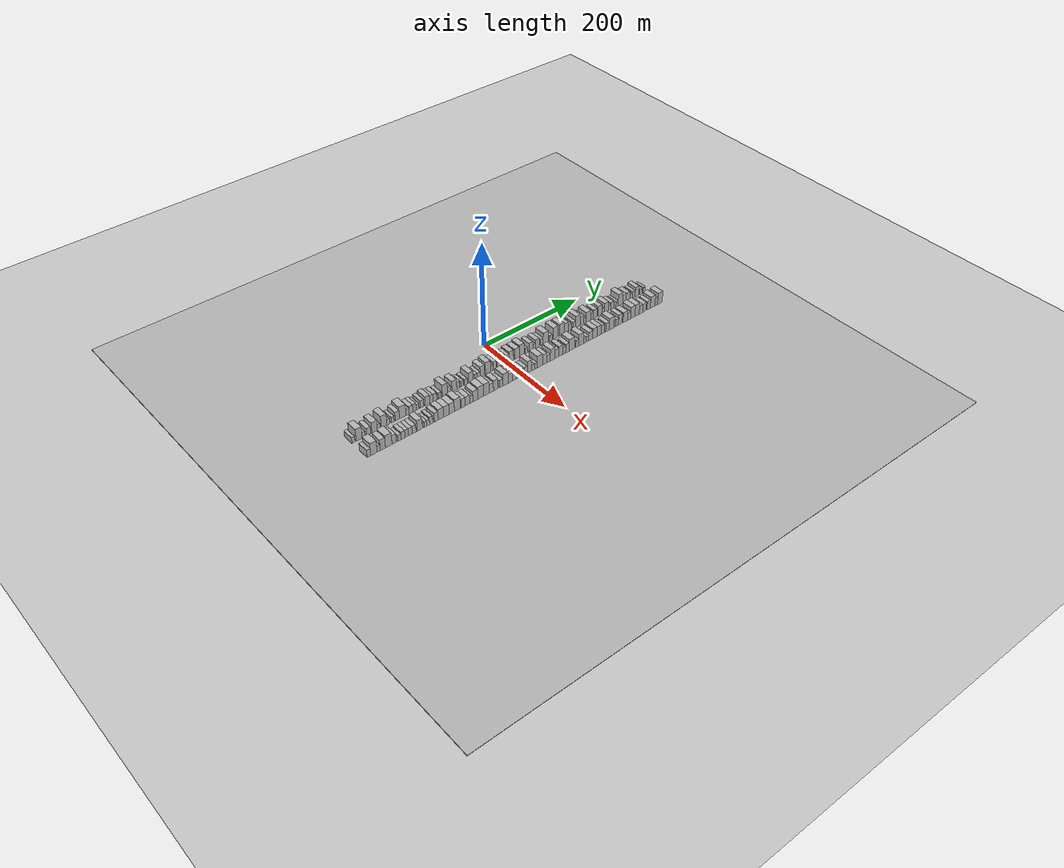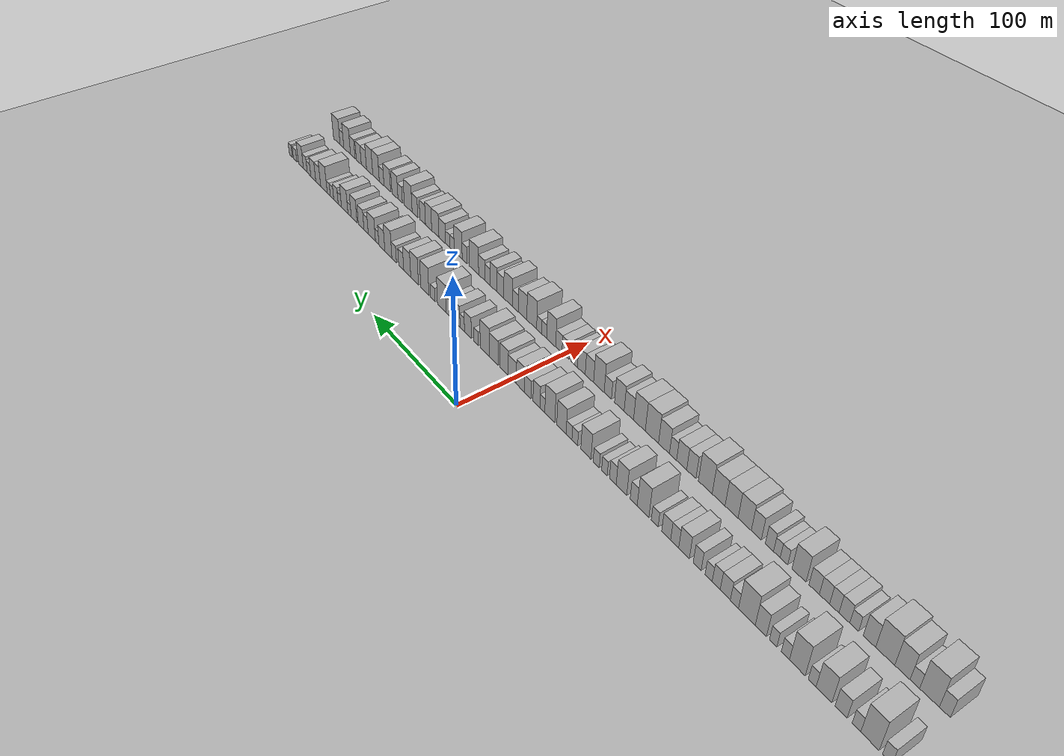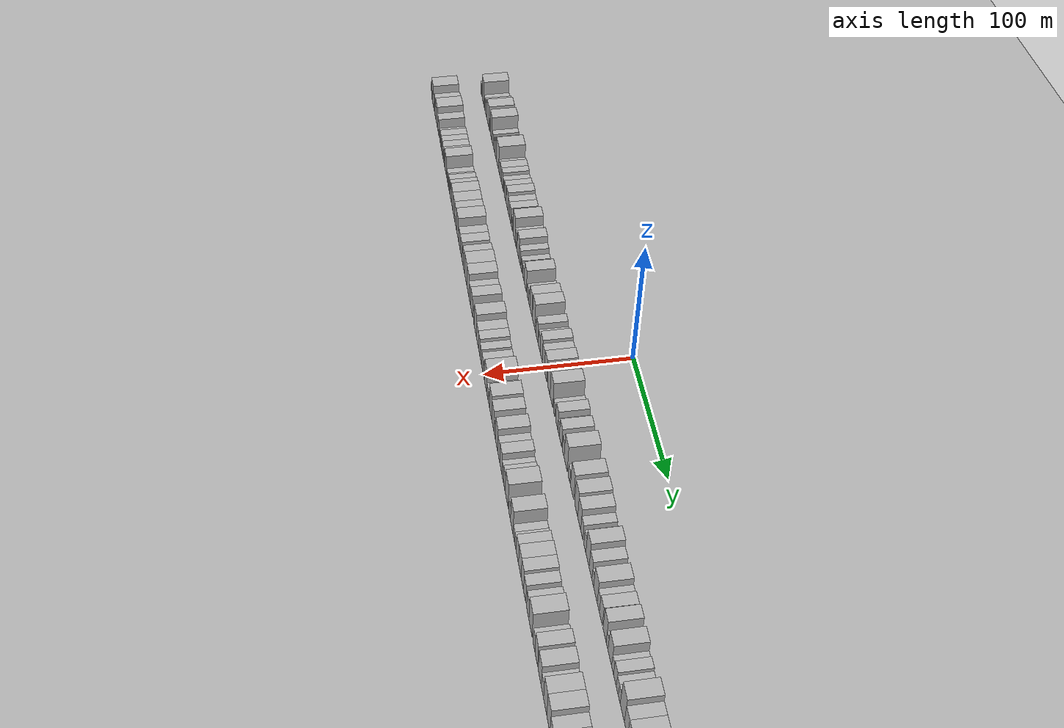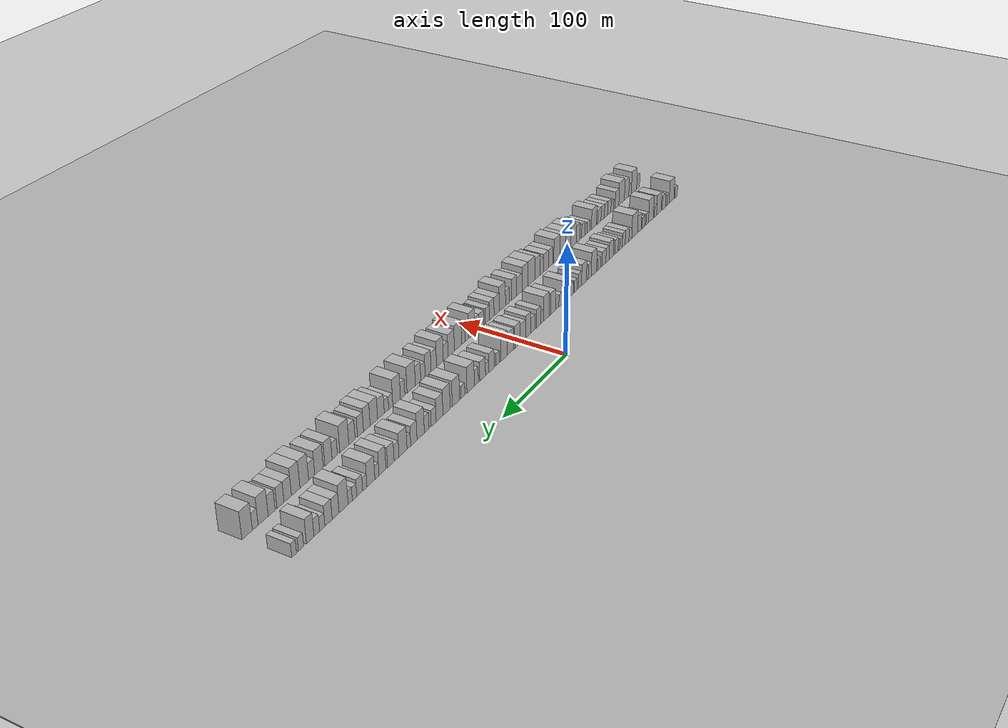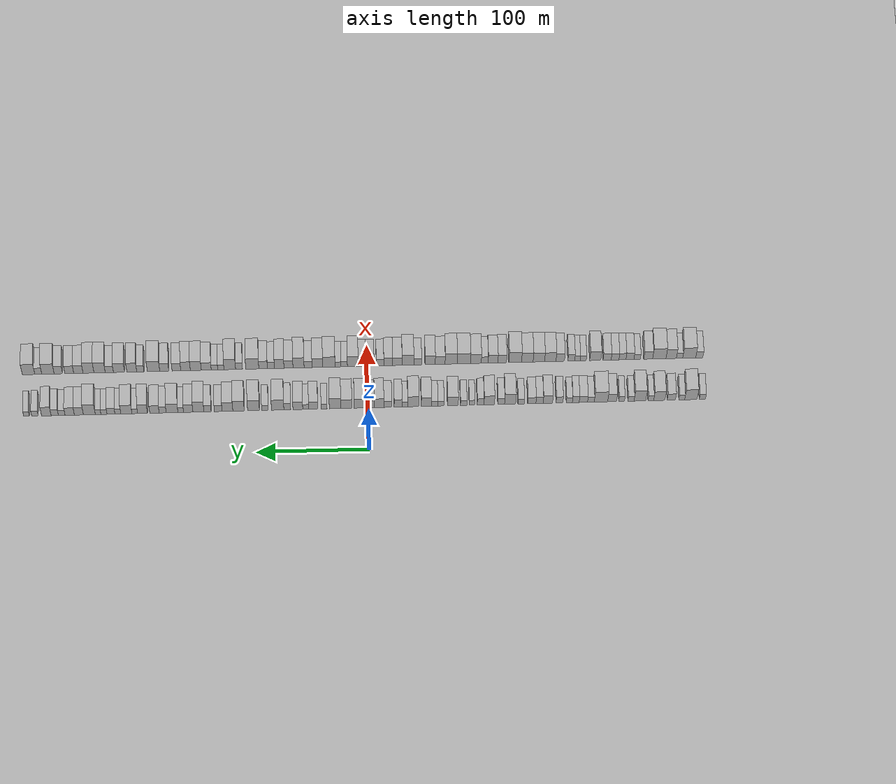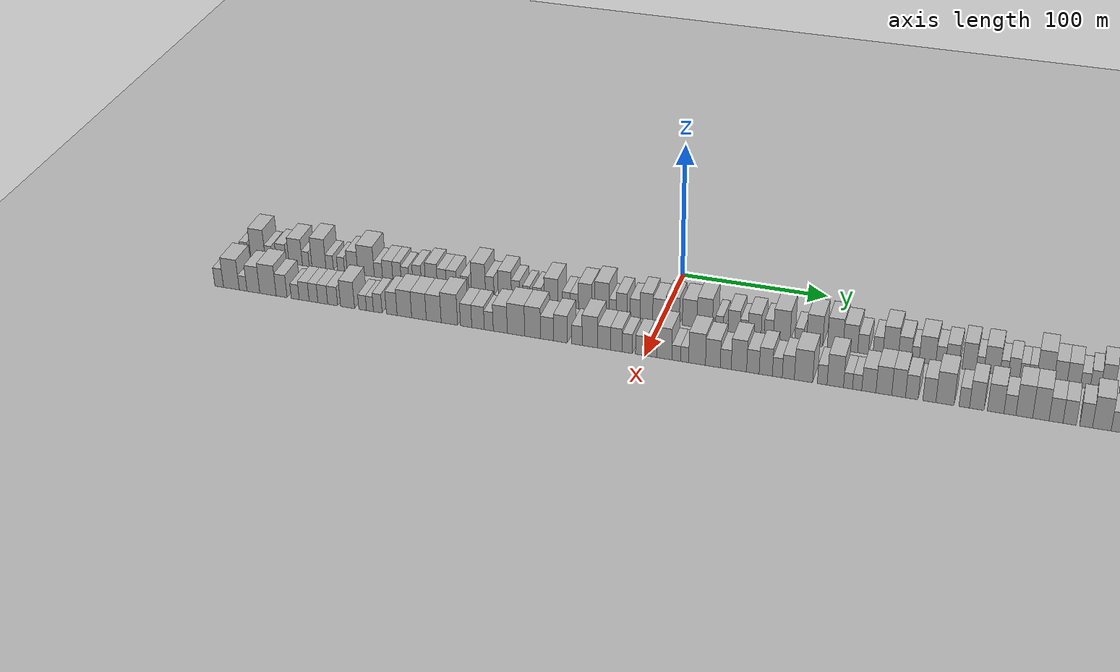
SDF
<?xml version="1.0" encoding="utf-8"?>

<sdf version="1.6">

   <world name="default">

      <gui fullscreen="0">

         <camera name="user_camera">

            <pose>-15 0 4.57585 0 0 0</pose>

            <view_controller>orbit</view_controller>

         </camera>

      </gui>

      <scene>

         <sky>

           <clouds>

             <speed>12</speed>

           </clouds>

         </sky>

         <ambient>0.4 0.4 0.4 1</ambient>

         <background>0.7 0.7 0.7 1</background>

         <shadows>1</shadows>

      </scene>

      <gravity>0 0 -9.8066</gravity>

      <magnetic_field>6e-06 2.3e-05 -4.2e-05</magnetic_field>

      <physics default="0" name="default_physics" type="ode">

         <ode>

            <solver>

               <type>quick</type>

               <iters>10</iters>

               <sor>1.0</sor>

               <use_dynamic_moi_rescaling>0</use_dynamic_moi_rescaling>

            </solver>

            <constraints>

               <cfm>0</cfm>

               <erp>0.2</erp>

               <contact_max_correcting_vel>100</contact_max_correcting_vel>

               <contact_surface_layer>0.001</contact_surface_layer>

            </constraints>

         </ode>

         <max_step_size>0.004</max_step_size>

         <real_time_factor>1</real_time_factor>

         <real_time_update_rate>250</real_time_update_rate>

      </physics>

      <light name="sun" type="directional">

         <cast_shadows>1</cast_shadows>

         <pose>0 0 10 0 0 0</pose>

         <diffuse>0.8 0.8 0.8 1</diffuse>

         <specular>0.2 0.2 0.2 1</specular>

         <attenuation>

            <range>1000</range>

            <constant>0.9</constant>

            <linear>0.01</linear>

            <quadratic>0.001</quadratic>

         </attenuation>

         <direction>-0.5 0.1 -0.9</direction>

      </light>

      <include>

         <name>ground_plane_1</name>

         <uri>model://HANNAS_ground_plane</uri>

         <pose>0 0 0  0 0 0</pose>

      </include>

      <include>

         <name>ground_plane_2</name>

         <uri>model://HANNAS_ground_plane</uri>

         <pose>100 0 0  0 0 0</pose>

      </include>

      <model name="building_1">

         <static>1</static>

         <pose frame="">50.0000 -297.1973 0 0.000000 0.000000 0.000000</pose>

         <link name="link">

            <pose frame="">0 0 6.00 0 0 0</pose>

            <collision name="collision">

               <geometry>

                  <box>

                     <size>20.0000 5.6054 12.0000</size>

                  </box>

               </geometry>

               <max_contacts>10</max_contacts>

               <surface>

                  <contact>

                     <ode/>

                  </contact>

                  <bounce/>

                  <friction>

                     <torsional>

                        <ode/>

                     </torsional>

                     <ode/>

                  </friction>

               </surface>

            </collision>

            <visual name="visual">

               <cast_shadows>0</cast_shadows>

               <geometry>

                  <box>

                     <size>20.0000 5.6054 12.0000</size>

                  </box>

               </geometry>

               <material>

                  <script>

                     <uri>model://HANNAS_wall/materials/scripts</uri>

                     <uri>model://HANNAS_wall/materials/textures</uri>

                     <name>vrc/HANNAS_wall</name>

                  </script>

               </material>

            </visual>

            <self_collide>0</self_collide>

            <enable_wind>0</enable_wind>

            <kinematic>0</kinematic>

         </link>

      </model>

      <model name="building_2">

         <static>1</static>

         <pose frame="">50.0000 -286.9371 0 0.000000 0.000000 0.000000</pose>

         <link name="link">

            <pose frame="">0 0 12.00 0 0 0</pose>

            <collision name="collision">

               <geometry>

                  <box>

                     <size>20.0000 10.9151 24.0000</size>

                  </box>

               </geometry>

               <max_contacts>10</max_contacts>

               <surface>

                  <contact>

                     <ode/>

                  </contact>

                  <bounce/>

                  <friction>

                     <torsional>

                        <ode/>

                     </torsional>

                     <ode/>

                  </friction>

               </surface>

            </collision>

            <visual name="visual">

               <cast_shadows>0</cast_shadows>

               <geometry>

                  <box>

                     <size>20.0000 10.9151 24.0000</size>

                  </box>

               </geometry>

               <material>

                  <script>

                     <uri>model://HANNAS_wall/materials/scripts</uri>

                     <uri>model://HANNAS_wall/materials/textures</uri>

                     <name>vrc/HANNAS_wall</name>

                  </script>

               </material>

            </visual>

            <self_collide>0</self_collide>

            <enable_wind>0</enable_wind>

            <kinematic>0</kinematic>

         </link>

      </model>

      <model name="building_3">

         <static>1</static>

         <pose frame="">50.0000 -278.8624 0 0.000000 0.000000 0.000000</pose>

         <link name="link">

            <pose frame="">0 0 6.00 0 0 0</pose>

            <collision name="collision">

               <geometry>

                  <box>

                     <size>20.0000 5.2342 12.0000</size>

                  </box>

               </geometry>

               <max_contacts>10</max_contacts>

               <surface>

                  <contact>

                     <ode/>

                  </contact>

                  <bounce/>

                  <friction>

                     <torsional>

                        <ode/>

                     </torsional>

                     <ode/>

                  </friction>

               </surface>

            </collision>

            <visual name="visual">

               <cast_shadows>0</cast_shadows>

               <geometry>

                  <box>

                     <size>20.0000 5.2342 12.0000</size>

                  </box>

               </geometry>

               <material>

                  <script>

                     <uri>model://HANNAS_wall/materials/scripts</uri>

                     <uri>model://HANNAS_wall/materials/textures</uri>

                     <name>vrc/HANNAS_wall</name>

                  </script>

               </material>

            </visual>

            <self_collide>0</self_collide>

            <enable_wind>0</enable_wind>

            <kinematic>0</kinematic>

         </link>

      </model>

      <model name="building_4">

         <static>1</static>

         <pose frame="">50.0000 -269.5270 0 0.000000 0.000000 0.000000</pose>

         <link name="link">

            <pose frame="">0 0 7.50 0 0 0</pose>

            <collision name="collision">

               <geometry>

                  <box>

                     <size>20.0000 7.4367 15.0000</size>

                  </box>

               </geometry>

               <max_contacts>10</max_contacts>

               <surface>

                  <contact>

                     <ode/>

                  </contact>

                  <bounce/>

                  <friction>

                     <torsional>

                        <ode/>

                     </torsional>

                     <ode/>

                  </friction>

               </surface>

            </collision>

            <visual name="visual">

               <cast_shadows>0</cast_shadows>

               <geometry>

                  <box>

                     <size>20.0000 7.4367 15.0000</size>

                  </box>

               </geometry>

               <material>

                  <script>

                     <uri>model://HANNAS_wall/materials/scripts</uri>

                     <uri>model://HANNAS_wall/materials/textures</uri>

                     <name>vrc/HANNAS_wall</name>

                  </script>

               </material>

            </visual>

            <self_collide>0</self_collide>

            <enable_wind>0</enable_wind>

            <kinematic>0</kinematic>

         </link>

      </model>

      <model name="building_5">

         <static>1</static>

         <pose frame="">50.0000 -258.8061 0 0.000000 0.000000 0.000000</pose>

         <link name="link">

            <pose frame="">0 0 10.50 0 0 0</pose>

            <collision name="collision">

               <geometry>

                  <box>

                     <size>20.0000 10.0052 21.0000</size>

                  </box>

               </geometry>

               <max_contacts>10</max_contacts>

               <surface>

                  <contact>

                     <ode/>

                  </contact>

                  <bounce/>

                  <friction>

                     <torsional>

                        <ode/>

                     </torsional>

                     <ode/>

                  </friction>

               </surface>

            </collision>

            <visual name="visual">

               <cast_shadows>0</cast_shadows>

               <geometry>

                  <box>

                     <size>20.0000 10.0052 21.0000</size>

                  </box>

               </geometry>

               <material>

                  <script>

                     <uri>model://HANNAS_wall/materials/scripts</uri>

                     <uri>model://HANNAS_wall/materials/textures</uri>

                     <name>vrc/HANNAS_wall</name>

                  </script>

               </material>

            </visual>

            <self_collide>0</self_collide>

            <enable_wind>0</enable_wind>

            <kinematic>0</kinematic>

         </link>

      </model>

      <model name="building_6">

         <static>1</static>

         <pose frame="">50.0000 -251.2828 0 0.000000 0.000000 0.000000</pose>

         <link name="link">

            <pose frame="">0 0 6.00 0 0 0</pose>

            <collision name="collision">

               <geometry>

                  <box>

                     <size>20.0000 5.0414 12.0000</size>

                  </box>

               </geometry>

               <max_contacts>10</max_contacts>

               <surface>

                  <contact>

                     <ode/>

                  </contact>

                  <bounce/>

                  <friction>

                     <torsional>

                        <ode/>

                     </torsional>

                     <ode/>

                  </friction>

               </surface>

            </collision>

            <visual name="visual">

               <cast_shadows>0</cast_shadows>

               <geometry>

                  <box>

                     <size>20.0000 5.0414 12.0000</size>

                  </box>

               </geometry>

               <material>

                  <script>

                     <uri>model://HANNAS_wall/materials/scripts</uri>

                     <uri>model://HANNAS_wall/materials/textures</uri>

                     <name>vrc/HANNAS_wall</name>

                  </script>

               </material>

            </visual>

            <self_collide>0</self_collide>

            <enable_wind>0</enable_wind>

            <kinematic>0</kinematic>

         </link>

      </model>

      <model name="building_7">

         <static>1</static>

         <pose frame="">50.0000 -241.5518 0 0.000000 0.000000 0.000000</pose>

         <link name="link">

            <pose frame="">0 0 12.00 0 0 0</pose>

            <collision name="collision">

               <geometry>

                  <box>

                     <size>20.0000 10.4205 24.0000</size>

                  </box>

               </geometry>

               <max_contacts>10</max_contacts>

               <surface>

                  <contact>

                     <ode/>

                  </contact>

                  <bounce/>

                  <friction>

                     <torsional>

                        <ode/>

                     </torsional>

                     <ode/>

                  </friction>

               </surface>

            </collision>

            <visual name="visual">

               <cast_shadows>0</cast_shadows>

               <geometry>

                  <box>

                     <size>20.0000 10.4205 24.0000</size>

                  </box>

               </geometry>

               <material>

                  <script>

                     <uri>model://HANNAS_wall/materials/scripts</uri>

                     <uri>model://HANNAS_wall/materials/textures</uri>

                     <name>vrc/HANNAS_wall</name>

                  </script>

               </material>

            </visual>

            <self_collide>0</self_collide>

            <enable_wind>0</enable_wind>

            <kinematic>0</kinematic>

         </link>

      </model>

      <model name="building_8">

         <static>1</static>

         <pose frame="">50.0000 -233.5852 0 0.000000 0.000000 0.000000</pose>

         <link name="link">

            <pose frame="">0 0 6.00 0 0 0</pose>

            <collision name="collision">

               <geometry>

                  <box>

                     <size>20.0000 5.5127 12.0000</size>

                  </box>

               </geometry>

               <max_contacts>10</max_contacts>

               <surface>

                  <contact>

                     <ode/>

                  </contact>

                  <bounce/>

                  <friction>

                     <torsional>

                        <ode/>

                     </torsional>

                     <ode/>

                  </friction>

               </surface>

            </collision>

            <visual name="visual">

               <cast_shadows>0</cast_shadows>

               <geometry>

                  <box>

                     <size>20.0000 5.5127 12.0000</size>

                  </box>

               </geometry>

               <material>

                  <script>

                     <uri>model://HANNAS_wall/materials/scripts</uri>

                     <uri>model://HANNAS_wall/materials/textures</uri>

                     <name>vrc/HANNAS_wall</name>

                  </script>

               </material>

            </visual>

            <self_collide>0</self_collide>

            <enable_wind>0</enable_wind>

            <kinematic>0</kinematic>

         </link>

      </model>

      <model name="building_9">

         <static>1</static>

         <pose frame="">50.0000 -225.2683 0 0.000000 0.000000 0.000000</pose>

         <link name="link">

            <pose frame="">0 0 6.00 0 0 0</pose>

            <collision name="collision">

               <geometry>

                  <box>

                     <size>20.0000 5.1211 12.0000</size>

                  </box>

               </geometry>

               <max_contacts>10</max_contacts>

               <surface>

                  <contact>

                     <ode/>

                  </contact>

                  <bounce/>

                  <friction>

                     <torsional>

                        <ode/>

                     </torsional>

                     <ode/>

                  </friction>

               </surface>

            </collision>

            <visual name="visual">

               <cast_shadows>0</cast_shadows>

               <geometry>

                  <box>

                     <size>20.0000 5.1211 12.0000</size>

                  </box>

               </geometry>

               <material>

                  <script>

                     <uri>model://HANNAS_wall/materials/scripts</uri>

                     <uri>model://HANNAS_wall/materials/textures</uri>

                     <name>vrc/HANNAS_wall</name>

                  </script>

               </material>

            </visual>

            <self_collide>0</self_collide>

            <enable_wind>0</enable_wind>

            <kinematic>0</kinematic>

         </link>

      </model>

      <model name="building_10">

         <static>1</static>

         <pose frame="">50.0000 -216.8005 0 0.000000 0.000000 0.000000</pose>

         <link name="link">

            <pose frame="">0 0 9.00 0 0 0</pose>

            <collision name="collision">

               <geometry>

                  <box>

                     <size>20.0000 7.8146 18.0000</size>

                  </box>

               </geometry>

               <max_contacts>10</max_contacts>

               <surface>

                  <contact>

                     <ode/>

                  </contact>

                  <bounce/>

                  <friction>

                     <torsional>

                        <ode/>

                     </torsional>

                     <ode/>

                  </friction>

               </surface>

            </collision>

            <visual name="visual">

               <cast_shadows>0</cast_shadows>

               <geometry>

                  <box>

                     <size>20.0000 7.8146 18.0000</size>

                  </box>

               </geometry>

               <material>

                  <script>

                     <uri>model://HANNAS_wall/materials/scripts</uri>

                     <uri>model://HANNAS_wall/materials/textures</uri>

                     <name>vrc/HANNAS_wall</name>

                  </script>

               </material>

            </visual>

            <self_collide>0</self_collide>

            <enable_wind>0</enable_wind>

            <kinematic>0</kinematic>

         </link>

      </model>

      <model name="building_11">

         <static>1</static>

         <pose frame="">50.0000 -206.9055 0 0.000000 0.000000 0.000000</pose>

         <link name="link">

            <pose frame="">0 0 12.00 0 0 0</pose>

            <collision name="collision">

               <geometry>

                  <box>

                     <size>20.0000 11.9755 24.0000</size>

                  </box>

               </geometry>

               <max_contacts>10</max_contacts>

               <surface>

                  <contact>

                     <ode/>

                  </contact>

                  <bounce/>

                  <friction>

                     <torsional>

                        <ode/>

                     </torsional>

                     <ode/>

                  </friction>

               </surface>

            </collision>

            <visual name="visual">

               <cast_shadows>0</cast_shadows>

               <geometry>

                  <box>

                     <size>20.0000 11.9755 24.0000</size>

                  </box>

               </geometry>

               <material>

                  <script>

                     <uri>model://HANNAS_wall/materials/scripts</uri>

                     <uri>model://HANNAS_wall/materials/textures</uri>

                     <name>vrc/HANNAS_wall</name>

                  </script>

               </material>

            </visual>

            <self_collide>0</self_collide>

            <enable_wind>0</enable_wind>

            <kinematic>0</kinematic>

         </link>

      </model>

      <model name="building_12">

         <static>1</static>

         <pose frame="">50.0000 -197.9457 0 0.000000 0.000000 0.000000</pose>

         <link name="link">

            <pose frame="">0 0 6.00 0 0 0</pose>

            <collision name="collision">

               <geometry>

                  <box>

                     <size>20.0000 5.9440 12.0000</size>

                  </box>

               </geometry>

               <max_contacts>10</max_contacts>

               <surface>

                  <contact>

                     <ode/>

                  </contact>

                  <bounce/>

                  <friction>

                     <torsional>

                        <ode/>

                     </torsional>

                     <ode/>

                  </friction>

               </surface>

            </collision>

            <visual name="visual">

               <cast_shadows>0</cast_shadows>

               <geometry>

                  <box>

                     <size>20.0000 5.9440 12.0000</size>

                  </box>

               </geometry>

               <material>

                  <script>

                     <uri>model://HANNAS_wall/materials/scripts</uri>

                     <uri>model://HANNAS_wall/materials/textures</uri>

                     <name>vrc/HANNAS_wall</name>

                  </script>

               </material>

            </visual>

            <self_collide>0</self_collide>

            <enable_wind>0</enable_wind>

            <kinematic>0</kinematic>

         </link>

      </model>

      <model name="building_13">

         <static>1</static>

         <pose frame="">50.0000 -191.2312 0 0.000000 0.000000 0.000000</pose>

         <link name="link">

            <pose frame="">0 0 7.50 0 0 0</pose>

            <collision name="collision">

               <geometry>

                  <box>

                     <size>20.0000 7.4850 15.0000</size>

                  </box>

               </geometry>

               <max_contacts>10</max_contacts>

               <surface>

                  <contact>

                     <ode/>

                  </contact>

                  <bounce/>

                  <friction>

                     <torsional>

                        <ode/>

                     </torsional>

                     <ode/>

                  </friction>

               </surface>

            </collision>

            <visual name="visual">

               <cast_shadows>0</cast_shadows>

               <geometry>

                  <box>

                     <size>20.0000 7.4850 15.0000</size>

                  </box>

               </geometry>

               <material>

                  <script>

                     <uri>model://HANNAS_wall/materials/scripts</uri>

                     <uri>model://HANNAS_wall/materials/textures</uri>

                     <name>vrc/HANNAS_wall</name>

                  </script>

               </material>

            </visual>

            <self_collide>0</self_collide>

            <enable_wind>0</enable_wind>

            <kinematic>0</kinematic>

         </link>

      </model>

      <model name="building_14">

         <static>1</static>

         <pose frame="">50.0000 -184.4612 0 0.000000 0.000000 0.000000</pose>

         <link name="link">

            <pose frame="">0 0 7.50 0 0 0</pose>

            <collision name="collision">

               <geometry>

                  <box>

                     <size>20.0000 6.0550 15.0000</size>

                  </box>

               </geometry>

               <max_contacts>10</max_contacts>

               <surface>

                  <contact>

                     <ode/>

                  </contact>

                  <bounce/>

                  <friction>

                     <torsional>

                        <ode/>

                     </torsional>

                     <ode/>

                  </friction>

               </surface>

            </collision>

            <visual name="visual">

               <cast_shadows>0</cast_shadows>

               <geometry>

                  <box>

                     <size>20.0000 6.0550 15.0000</size>

                  </box>

               </geometry>

               <material>

                  <script>

                     <uri>model://HANNAS_wall/materials/scripts</uri>

                     <uri>model://HANNAS_wall/materials/textures</uri>

                     <name>vrc/HANNAS_wall</name>

                  </script>

               </material>

            </visual>

            <self_collide>0</self_collide>

            <enable_wind>0</enable_wind>

            <kinematic>0</kinematic>

         </link>

      </model>

      <model name="building_15">

         <static>1</static>

         <pose frame="">50.0000 -178.7325 0 0.000000 0.000000 0.000000</pose>

         <link name="link">

            <pose frame="">0 0 6.00 0 0 0</pose>

            <collision name="collision">

               <geometry>

                  <box>

                     <size>20.0000 5.4024 12.0000</size>

                  </box>

               </geometry>

               <max_contacts>10</max_contacts>

               <surface>

                  <contact>

                     <ode/>

                  </contact>

                  <bounce/>

                  <friction>

                     <torsional>

                        <ode/>

                     </torsional>

                     <ode/>

                  </friction>

               </surface>

            </collision>

            <visual name="visual">

               <cast_shadows>0</cast_shadows>

               <geometry>

                  <box>

                     <size>20.0000 5.4024 12.0000</size>

                  </box>

               </geometry>

               <material>

                  <script>

                     <uri>model://HANNAS_wall/materials/scripts</uri>

                     <uri>model://HANNAS_wall/materials/textures</uri>

                     <name>vrc/HANNAS_wall</name>

                  </script>

               </material>

            </visual>

            <self_collide>0</self_collide>

            <enable_wind>0</enable_wind>

            <kinematic>0</kinematic>

         </link>

      </model>

      <model name="building_16">

         <static>1</static>

         <pose frame="">50.0000 -169.9344 0 0.000000 0.000000 0.000000</pose>

         <link name="link">

            <pose frame="">0 0 7.50 0 0 0</pose>

            <collision name="collision">

               <geometry>

                  <box>

                     <size>20.0000 6.1939 15.0000</size>

                  </box>

               </geometry>

               <max_contacts>10</max_contacts>

               <surface>

                  <contact>

                     <ode/>

                  </contact>

                  <bounce/>

                  <friction>

                     <torsional>

                        <ode/>

                     </torsional>

                     <ode/>

                  </friction>

               </surface>

            </collision>

            <visual name="visual">

               <cast_shadows>0</cast_shadows>

               <geometry>

                  <box>

                     <size>20.0000 6.1939 15.0000</size>

                  </box>

               </geometry>

               <material>

                  <script>

                     <uri>model://HANNAS_wall/materials/scripts</uri>

                     <uri>model://HANNAS_wall/materials/textures</uri>

                     <name>vrc/HANNAS_wall</name>

                  </script>

               </material>

            </visual>

            <self_collide>0</self_collide>

            <enable_wind>0</enable_wind>

            <kinematic>0</kinematic>

         </link>

      </model>

      <model name="building_17">

         <static>1</static>

         <pose frame="">50.0000 -159.6488 0 0.000000 0.000000 0.000000</pose>

         <link name="link">

            <pose frame="">0 0 9.00 0 0 0</pose>

            <collision name="collision">

               <geometry>

                  <box>

                     <size>20.0000 8.3773 18.0000</size>

                  </box>

               </geometry>

               <max_contacts>10</max_contacts>

               <surface>

                  <contact>

                     <ode/>

                  </contact>

                  <bounce/>

                  <friction>

                     <torsional>

                        <ode/>

                     </torsional>

                     <ode/>

                  </friction>

               </surface>

            </collision>

            <visual name="visual">

               <cast_shadows>0</cast_shadows>

               <geometry>

                  <box>

                     <size>20.0000 8.3773 18.0000</size>

                  </box>

               </geometry>

               <material>

                  <script>

                     <uri>model://HANNAS_wall/materials/scripts</uri>

                     <uri>model://HANNAS_wall/materials/textures</uri>

                     <name>vrc/HANNAS_wall</name>

                  </script>

               </material>

            </visual>

            <self_collide>0</self_collide>

            <enable_wind>0</enable_wind>

            <kinematic>0</kinematic>

         </link>

      </model>

      <model name="building_18">

         <static>1</static>

         <pose frame="">50.0000 -152.2264 0 0.000000 0.000000 0.000000</pose>

         <link name="link">

            <pose frame="">0 0 7.50 0 0 0</pose>

            <collision name="collision">

               <geometry>

                  <box>

                     <size>20.0000 6.4675 15.0000</size>

                  </box>

               </geometry>

               <max_contacts>10</max_contacts>

               <surface>

                  <contact>

                     <ode/>

                  </contact>

                  <bounce/>

                  <friction>

                     <torsional>

                        <ode/>

                     </torsional>

                     <ode/>

                  </friction>

               </surface>

            </collision>

            <visual name="visual">

               <cast_shadows>0</cast_shadows>

               <geometry>

                  <box>

                     <size>20.0000 6.4675 15.0000</size>

                  </box>

               </geometry>

               <material>

                  <script>

                     <uri>model://HANNAS_wall/materials/scripts</uri>

                     <uri>model://HANNAS_wall/materials/textures</uri>

                     <name>vrc/HANNAS_wall</name>

                  </script>

               </material>

            </visual>

            <self_collide>0</self_collide>

            <enable_wind>0</enable_wind>

            <kinematic>0</kinematic>

         </link>

      </model>

      <model name="building_19">

         <static>1</static>

         <pose frame="">50.0000 -145.3446 0 0.000000 0.000000 0.000000</pose>

         <link name="link">

            <pose frame="">0 0 7.50 0 0 0</pose>

            <collision name="collision">

               <geometry>

                  <box>

                     <size>20.0000 7.2962 15.0000</size>

                  </box>

               </geometry>

               <max_contacts>10</max_contacts>

               <surface>

                  <contact>

                     <ode/>

                  </contact>

                  <bounce/>

                  <friction>

                     <torsional>

                        <ode/>

                     </torsional>

                     <ode/>

                  </friction>

               </surface>

            </collision>

            <visual name="visual">

               <cast_shadows>0</cast_shadows>

               <geometry>

                  <box>

                     <size>20.0000 7.2962 15.0000</size>

                  </box>

               </geometry>

               <material>

                  <script>

                     <uri>model://HANNAS_wall/materials/scripts</uri>

                     <uri>model://HANNAS_wall/materials/textures</uri>

                     <name>vrc/HANNAS_wall</name>

                  </script>

               </material>

            </visual>

            <self_collide>0</self_collide>

            <enable_wind>0</enable_wind>

            <kinematic>0</kinematic>

         </link>

      </model>

      <model name="building_20">

         <static>1</static>

         <pose frame="">50.0000 -135.8455 0 0.000000 0.000000 0.000000</pose>

         <link name="link">

            <pose frame="">0 0 6.00 0 0 0</pose>

            <collision name="collision">

               <geometry>

                  <box>

                     <size>20.0000 5.7019 12.0000</size>

                  </box>

               </geometry>

               <max_contacts>10</max_contacts>

               <surface>

                  <contact>

                     <ode/>

                  </contact>

                  <bounce/>

                  <friction>

                     <torsional>

                        <ode/>

                     </torsional>

                     <ode/>

                  </friction>

               </surface>

            </collision>

            <visual name="visual">

               <cast_shadows>0</cast_shadows>

               <geometry>

                  <box>

                     <size>20.0000 5.7019 12.0000</size>

                  </box>

               </geometry>

               <material>

                  <script>

                     <uri>model://HANNAS_wall/materials/scripts</uri>

                     <uri>model://HANNAS_wall/materials/textures</uri>

                     <name>vrc/HANNAS_wall</name>

                  </script>

               </material>

            </visual>

            <self_collide>0</self_collide>

            <enable_wind>0</enable_wind>

            <kinematic>0</kinematic>

         </link>

      </model>

      <model name="building_21">

         <static>1</static>

         <pose frame="">50.0000 -126.0394 0 0.000000 0.000000 0.000000</pose>

         <link name="link">

            <pose frame="">0 0 12.00 0 0 0</pose>

            <collision name="collision">

               <geometry>

                  <box>

                     <size>20.0000 9.9102 24.0000</size>

                  </box>

               </geometry>

               <max_contacts>10</max_contacts>

               <surface>

                  <contact>

                     <ode/>

                  </contact>

                  <bounce/>

                  <friction>

                     <torsional>

                        <ode/>

                     </torsional>

                     <ode/>

                  </friction>

               </surface>

            </collision>

            <visual name="visual">

               <cast_shadows>0</cast_shadows>

               <geometry>

                  <box>

                     <size>20.0000 9.9102 24.0000</size>

                  </box>

               </geometry>

               <material>

                  <script>

                     <uri>model://HANNAS_wall/materials/scripts</uri>

                     <uri>model://HANNAS_wall/materials/textures</uri>

                     <name>vrc/HANNAS_wall</name>

                  </script>

               </material>

            </visual>

            <self_collide>0</self_collide>

            <enable_wind>0</enable_wind>

            <kinematic>0</kinematic>

         </link>

      </model>

      <model name="building_22">

         <static>1</static>

         <pose frame="">50.0000 -118.0736 0 0.000000 0.000000 0.000000</pose>

         <link name="link">

            <pose frame="">0 0 7.50 0 0 0</pose>

            <collision name="collision">

               <geometry>

                  <box>

                     <size>20.0000 6.0215 15.0000</size>

                  </box>

               </geometry>

               <max_contacts>10</max_contacts>

               <surface>

                  <contact>

                     <ode/>

                  </contact>

                  <bounce/>

                  <friction>

                     <torsional>

                        <ode/>

                     </torsional>

                     <ode/>

                  </friction>

               </surface>

            </collision>

            <visual name="visual">

               <cast_shadows>0</cast_shadows>

               <geometry>

                  <box>

                     <size>20.0000 6.0215 15.0000</size>

                  </box>

               </geometry>

               <material>

                  <script>

                     <uri>model://HANNAS_wall/materials/scripts</uri>

                     <uri>model://HANNAS_wall/materials/textures</uri>

                     <name>vrc/HANNAS_wall</name>

                  </script>

               </material>

            </visual>

            <self_collide>0</self_collide>

            <enable_wind>0</enable_wind>

            <kinematic>0</kinematic>

         </link>

      </model>

      <model name="building_23">

         <static>1</static>

         <pose frame="">50.0000 -107.4133 0 0.000000 0.000000 0.000000</pose>

         <link name="link">

            <pose frame="">0 0 10.50 0 0 0</pose>

            <collision name="collision">

               <geometry>

                  <box>

                     <size>20.0000 9.2990 21.0000</size>

                  </box>

               </geometry>

               <max_contacts>10</max_contacts>

               <surface>

                  <contact>

                     <ode/>

                  </contact>

                  <bounce/>

                  <friction>

                     <torsional>

                        <ode/>

                     </torsional>

                     <ode/>

                  </friction>

               </surface>

            </collision>

            <visual name="visual">

               <cast_shadows>0</cast_shadows>

               <geometry>

                  <box>

                     <size>20.0000 9.2990 21.0000</size>

                  </box>

               </geometry>

               <material>

                  <script>

                     <uri>model://HANNAS_wall/materials/scripts</uri>

                     <uri>model://HANNAS_wall/materials/textures</uri>

                     <name>vrc/HANNAS_wall</name>

                  </script>

               </material>

            </visual>

            <self_collide>0</self_collide>

            <enable_wind>0</enable_wind>

            <kinematic>0</kinematic>

         </link>

      </model>

      <model name="building_24">

         <static>1</static>

         <pose frame="">50.0000 -99.7550 0 0.000000 0.000000 0.000000</pose>

         <link name="link">

            <pose frame="">0 0 7.50 0 0 0</pose>

            <collision name="collision">

               <geometry>

                  <box>

                     <size>20.0000 6.0176 15.0000</size>

                  </box>

               </geometry>

               <max_contacts>10</max_contacts>

               <surface>

                  <contact>

                     <ode/>

                  </contact>

                  <bounce/>

                  <friction>

                     <torsional>

                        <ode/>

                     </torsional>

                     <ode/>

                  </friction>

               </surface>

            </collision>

            <visual name="visual">

               <cast_shadows>0</cast_shadows>

               <geometry>

                  <box>

                     <size>20.0000 6.0176 15.0000</size>

                  </box>

               </geometry>

               <material>

                  <script>

                     <uri>model://HANNAS_wall/materials/scripts</uri>

                     <uri>model://HANNAS_wall/materials/textures</uri>

                     <name>vrc/HANNAS_wall</name>

                  </script>

               </material>

            </visual>

            <self_collide>0</self_collide>

            <enable_wind>0</enable_wind>

            <kinematic>0</kinematic>

         </link>

      </model>

      <model name="building_25">

         <static>1</static>

         <pose frame="">50.0000 -92.1950 0 0.000000 0.000000 0.000000</pose>

         <link name="link">

            <pose frame="">0 0 6.00 0 0 0</pose>

            <collision name="collision">

               <geometry>

                  <box>

                     <size>20.0000 5.1025 12.0000</size>

                  </box>

               </geometry>

               <max_contacts>10</max_contacts>

               <surface>

                  <contact>

                     <ode/>

                  </contact>

                  <bounce/>

                  <friction>

                     <torsional>

                        <ode/>

                     </torsional>

                     <ode/>

                  </friction>

               </surface>

            </collision>

            <visual name="visual">

               <cast_shadows>0</cast_shadows>

               <geometry>

                  <box>

                     <size>20.0000 5.1025 12.0000</size>

                  </box>

               </geometry>

               <material>

                  <script>

                     <uri>model://HANNAS_wall/materials/scripts</uri>

                     <uri>model://HANNAS_wall/materials/textures</uri>

                     <name>vrc/HANNAS_wall</name>

                  </script>

               </material>

            </visual>

            <self_collide>0</self_collide>

            <enable_wind>0</enable_wind>

            <kinematic>0</kinematic>

         </link>

      </model>

      <model name="building_26">

         <static>1</static>

         <pose frame="">50.0000 -84.7635 0 0.000000 0.000000 0.000000</pose>

         <link name="link">

            <pose frame="">0 0 6.00 0 0 0</pose>

            <collision name="collision">

               <geometry>

                  <box>

                     <size>20.0000 5.7605 12.0000</size>

                  </box>

               </geometry>

               <max_contacts>10</max_contacts>

               <surface>

                  <contact>

                     <ode/>

                  </contact>

                  <bounce/>

                  <friction>

                     <torsional>

                        <ode/>

                     </torsional>

                     <ode/>

                  </friction>

               </surface>

            </collision>

            <visual name="visual">

               <cast_shadows>0</cast_shadows>

               <geometry>

                  <box>

                     <size>20.0000 5.7605 12.0000</size>

                  </box>

               </geometry>

               <material>

                  <script>

                     <uri>model://HANNAS_wall/materials/scripts</uri>

                     <uri>model://HANNAS_wall/materials/textures</uri>

                     <name>vrc/HANNAS_wall</name>

                  </script>

               </material>

            </visual>

            <self_collide>0</self_collide>

            <enable_wind>0</enable_wind>

            <kinematic>0</kinematic>

         </link>

      </model>

      <model name="building_27">

         <static>1</static>

         <pose frame="">50.0000 -75.1036 0 0.000000 0.000000 0.000000</pose>

         <link name="link">

            <pose frame="">0 0 10.50 0 0 0</pose>

            <collision name="collision">

               <geometry>

                  <box>

                     <size>20.0000 9.5592 21.0000</size>

                  </box>

               </geometry>

               <max_contacts>10</max_contacts>

               <surface>

                  <contact>

                     <ode/>

                  </contact>

                  <bounce/>

                  <friction>

                     <torsional>

                        <ode/>

                     </torsional>

                     <ode/>

                  </friction>

               </surface>

            </collision>

            <visual name="visual">

               <cast_shadows>0</cast_shadows>

               <geometry>

                  <box>

                     <size>20.0000 9.5592 21.0000</size>

                  </box>

               </geometry>

               <material>

                  <script>

                     <uri>model://HANNAS_wall/materials/scripts</uri>

                     <uri>model://HANNAS_wall/materials/textures</uri>

                     <name>vrc/HANNAS_wall</name>

                  </script>

               </material>

            </visual>

            <self_collide>0</self_collide>

            <enable_wind>0</enable_wind>

            <kinematic>0</kinematic>

         </link>

      </model>

      <model name="building_28">

         <static>1</static>

         <pose frame="">50.0000 -64.5935 0 0.000000 0.000000 0.000000</pose>

         <link name="link">

            <pose frame="">0 0 6.00 0 0 0</pose>

            <collision name="collision">

               <geometry>

                  <box>

                     <size>20.0000 5.4610 12.0000</size>

                  </box>

               </geometry>

               <max_contacts>10</max_contacts>

               <surface>

                  <contact>

                     <ode/>

                  </contact>

                  <bounce/>

                  <friction>

                     <torsional>

                        <ode/>

                     </torsional>

                     <ode/>

                  </friction>

               </surface>

            </collision>

            <visual name="visual">

               <cast_shadows>0</cast_shadows>

               <geometry>

                  <box>

                     <size>20.0000 5.4610 12.0000</size>

                  </box>

               </geometry>

               <material>

                  <script>

                     <uri>model://HANNAS_wall/materials/scripts</uri>

                     <uri>model://HANNAS_wall/materials/textures</uri>

                     <name>vrc/HANNAS_wall</name>

                  </script>

               </material>

            </visual>

            <self_collide>0</self_collide>

            <enable_wind>0</enable_wind>

            <kinematic>0</kinematic>

         </link>

      </model>

      <model name="building_29">

         <static>1</static>

         <pose frame="">50.0000 -59.0190 0 0.000000 0.000000 0.000000</pose>

         <link name="link">

            <pose frame="">0 0 6.00 0 0 0</pose>

            <collision name="collision">

               <geometry>

                  <box>

                     <size>20.0000 5.6881 12.0000</size>

                  </box>

               </geometry>

               <max_contacts>10</max_contacts>

               <surface>

                  <contact>

                     <ode/>

                  </contact>

                  <bounce/>

                  <friction>

                     <torsional>

                        <ode/>

                     </torsional>

                     <ode/>

                  </friction>

               </surface>

            </collision>

            <visual name="visual">

               <cast_shadows>0</cast_shadows>

               <geometry>

                  <box>

                     <size>20.0000 5.6881 12.0000</size>

                  </box>

               </geometry>

               <material>

                  <script>

                     <uri>model://HANNAS_wall/materials/scripts</uri>

                     <uri>model://HANNAS_wall/materials/textures</uri>

                     <name>vrc/HANNAS_wall</name>

                  </script>

               </material>

            </visual>

            <self_collide>0</self_collide>

            <enable_wind>0</enable_wind>

            <kinematic>0</kinematic>

         </link>

      </model>

      <model name="building_30">

         <static>1</static>

         <pose frame="">50.0000 -51.6029 0 0.000000 0.000000 0.000000</pose>

         <link name="link">

            <pose frame="">0 0 10.50 0 0 0</pose>

            <collision name="collision">

               <geometry>

                  <box>

                     <size>20.0000 9.1441 21.0000</size>

                  </box>

               </geometry>

               <max_contacts>10</max_contacts>

               <surface>

                  <contact>

                     <ode/>

                  </contact>

                  <bounce/>

                  <friction>

                     <torsional>

                        <ode/>

                     </torsional>

                     <ode/>

                  </friction>

               </surface>

            </collision>

            <visual name="visual">

               <cast_shadows>0</cast_shadows>

               <geometry>

                  <box>

                     <size>20.0000 9.1441 21.0000</size>

                  </box>

               </geometry>

               <material>

                  <script>

                     <uri>model://HANNAS_wall/materials/scripts</uri>

                     <uri>model://HANNAS_wall/materials/textures</uri>

                     <name>vrc/HANNAS_wall</name>

                  </script>

               </material>

            </visual>

            <self_collide>0</self_collide>

            <enable_wind>0</enable_wind>

            <kinematic>0</kinematic>

         </link>

      </model>

      <model name="building_31">

         <static>1</static>

         <pose frame="">50.0000 -40.0426 0 0.000000 0.000000 0.000000</pose>

         <link name="link">

            <pose frame="">0 0 12.00 0 0 0</pose>

            <collision name="collision">

               <geometry>

                  <box>

                     <size>20.0000 9.9766 24.0000</size>

                  </box>

               </geometry>

               <max_contacts>10</max_contacts>

               <surface>

                  <contact>

                     <ode/>

                  </contact>

                  <bounce/>

                  <friction>

                     <torsional>

                        <ode/>

                     </torsional>

                     <ode/>

                  </friction>

               </surface>

            </collision>

            <visual name="visual">

               <cast_shadows>0</cast_shadows>

               <geometry>

                  <box>

                     <size>20.0000 9.9766 24.0000</size>

                  </box>

               </geometry>

               <material>

                  <script>

                     <uri>model://HANNAS_wall/materials/scripts</uri>

                     <uri>model://HANNAS_wall/materials/textures</uri>

                     <name>vrc/HANNAS_wall</name>

                  </script>

               </material>

            </visual>

            <self_collide>0</self_collide>

            <enable_wind>0</enable_wind>

            <kinematic>0</kinematic>

         </link>

      </model>

      <model name="building_32">

         <static>1</static>

         <pose frame="">50.0000 -32.5910 0 0.000000 0.000000 0.000000</pose>

         <link name="link">

            <pose frame="">0 0 6.00 0 0 0</pose>

            <collision name="collision">

               <geometry>

                  <box>

                     <size>20.0000 4.9266 12.0000</size>

                  </box>

               </geometry>

               <max_contacts>10</max_contacts>

               <surface>

                  <contact>

                     <ode/>

                  </contact>

                  <bounce/>

                  <friction>

                     <torsional>

                        <ode/>

                     </torsional>

                     <ode/>

                  </friction>

               </surface>

            </collision>

            <visual name="visual">

               <cast_shadows>0</cast_shadows>

               <geometry>

                  <box>

                     <size>20.0000 4.9266 12.0000</size>

                  </box>

               </geometry>

               <material>

                  <script>

                     <uri>model://HANNAS_wall/materials/scripts</uri>

                     <uri>model://HANNAS_wall/materials/textures</uri>

                     <name>vrc/HANNAS_wall</name>

                  </script>

               </material>

            </visual>

            <self_collide>0</self_collide>

            <enable_wind>0</enable_wind>

            <kinematic>0</kinematic>

         </link>

      </model>

      <model name="building_33">

         <static>1</static>

         <pose frame="">50.0000 -26.5214 0 0.000000 0.000000 0.000000</pose>

         <link name="link">

            <pose frame="">0 0 9.00 0 0 0</pose>

            <collision name="collision">

               <geometry>

                  <box>

                     <size>20.0000 7.2126 18.0000</size>

                  </box>

               </geometry>

               <max_contacts>10</max_contacts>

               <surface>

                  <contact>

                     <ode/>

                  </contact>

                  <bounce/>

                  <friction>

                     <torsional>

                        <ode/>

                     </torsional>

                     <ode/>

                  </friction>

               </surface>

            </collision>

            <visual name="visual">

               <cast_shadows>0</cast_shadows>

               <geometry>

                  <box>

                     <size>20.0000 7.2126 18.0000</size>

                  </box>

               </geometry>

               <material>

                  <script>

                     <uri>model://HANNAS_wall/materials/scripts</uri>

                     <uri>model://HANNAS_wall/materials/textures</uri>

                     <name>vrc/HANNAS_wall</name>

                  </script>

               </material>

            </visual>

            <self_collide>0</self_collide>

            <enable_wind>0</enable_wind>

            <kinematic>0</kinematic>

         </link>

      </model>

      <model name="building_34">

         <static>1</static>

         <pose frame="">50.0000 -17.3667 0 0.000000 0.000000 0.000000</pose>

         <link name="link">

            <pose frame="">0 0 7.50 0 0 0</pose>

            <collision name="collision">

               <geometry>

                  <box>

                     <size>20.0000 7.0967 15.0000</size>

                  </box>

               </geometry>

               <max_contacts>10</max_contacts>

               <surface>

                  <contact>

                     <ode/>

                  </contact>

                  <bounce/>

                  <friction>

                     <torsional>

                        <ode/>

                     </torsional>

                     <ode/>

                  </friction>

               </surface>

            </collision>

            <visual name="visual">

               <cast_shadows>0</cast_shadows>

               <geometry>

                  <box>

                     <size>20.0000 7.0967 15.0000</size>

                  </box>

               </geometry>

               <material>

                  <script>

                     <uri>model://HANNAS_wall/materials/scripts</uri>

                     <uri>model://HANNAS_wall/materials/textures</uri>

                     <name>vrc/HANNAS_wall</name>

                  </script>

               </material>

            </visual>

            <self_collide>0</self_collide>

            <enable_wind>0</enable_wind>

            <kinematic>0</kinematic>

         </link>

      </model>

      <model name="building_35">

         <static>1</static>

         <pose frame="">50.0000 -9.6184 0 0.000000 0.000000 0.000000</pose>

         <link name="link">

            <pose frame="">0 0 10.50 0 0 0</pose>

            <collision name="collision">

               <geometry>

                  <box>

                     <size>20.0000 8.4000 21.0000</size>

                  </box>

               </geometry>

               <max_contacts>10</max_contacts>

               <surface>

                  <contact>

                     <ode/>

                  </contact>

                  <bounce/>

                  <friction>

                     <torsional>

                        <ode/>

                     </torsional>

                     <ode/>

                  </friction>

               </surface>

            </collision>

            <visual name="visual">

               <cast_shadows>0</cast_shadows>

               <geometry>

                  <box>

                     <size>20.0000 8.4000 21.0000</size>

                  </box>

               </geometry>

               <material>

                  <script>

                     <uri>model://HANNAS_wall/materials/scripts</uri>

                     <uri>model://HANNAS_wall/materials/textures</uri>

                     <name>vrc/HANNAS_wall</name>

                  </script>

               </material>

            </visual>

            <self_collide>0</self_collide>

            <enable_wind>0</enable_wind>

            <kinematic>0</kinematic>

         </link>

      </model>

      <model name="building_36">

         <static>1</static>

         <pose frame="">50.0000 -1.0348 0 0.000000 0.000000 0.000000</pose>

         <link name="link">

            <pose frame="">0 0 9.00 0 0 0</pose>

            <collision name="collision">

               <geometry>

                  <box>

                     <size>20.0000 8.7670 18.0000</size>

                  </box>

               </geometry>

               <max_contacts>10</max_contacts>

               <surface>

                  <contact>

                     <ode/>

                  </contact>

                  <bounce/>

                  <friction>

                     <torsional>

                        <ode/>

                     </torsional>

                     <ode/>

                  </friction>

               </surface>

            </collision>

            <visual name="visual">

               <cast_shadows>0</cast_shadows>

               <geometry>

                  <box>

                     <size>20.0000 8.7670 18.0000</size>

                  </box>

               </geometry>

               <material>

                  <script>

                     <uri>model://HANNAS_wall/materials/scripts</uri>

                     <uri>model://HANNAS_wall/materials/textures</uri>

                     <name>vrc/HANNAS_wall</name>

                  </script>

               </material>

            </visual>

            <self_collide>0</self_collide>

            <enable_wind>0</enable_wind>

            <kinematic>0</kinematic>

         </link>

      </model>

      <model name="building_37">

         <static>1</static>

         <pose frame="">50.0000 7.9456 0 0.000000 0.000000 0.000000</pose>

         <link name="link">

            <pose frame="">0 0 10.50 0 0 0</pose>

            <collision name="collision">

               <geometry>

                  <box>

                     <size>20.0000 9.1939 21.0000</size>

                  </box>

               </geometry>

               <max_contacts>10</max_contacts>

               <surface>

                  <contact>

                     <ode/>

                  </contact>

                  <bounce/>

                  <friction>

                     <torsional>

                        <ode/>

                     </torsional>

                     <ode/>

                  </friction>

               </surface>

            </collision>

            <visual name="visual">

               <cast_shadows>0</cast_shadows>

               <geometry>

                  <box>

                     <size>20.0000 9.1939 21.0000</size>

                  </box>

               </geometry>

               <material>

                  <script>

                     <uri>model://HANNAS_wall/materials/scripts</uri>

                     <uri>model://HANNAS_wall/materials/textures</uri>

                     <name>vrc/HANNAS_wall</name>

                  </script>

               </material>

            </visual>

            <self_collide>0</self_collide>

            <enable_wind>0</enable_wind>

            <kinematic>0</kinematic>

         </link>

      </model>

      <model name="building_38">

         <static>1</static>

         <pose frame="">50.0000 19.4693 0 0.000000 0.000000 0.000000</pose>

         <link name="link">

            <pose frame="">0 0 10.50 0 0 0</pose>

            <collision name="collision">

               <geometry>

                  <box>

                     <size>20.0000 9.8533 21.0000</size>

                  </box>

               </geometry>

               <max_contacts>10</max_contacts>

               <surface>

                  <contact>

                     <ode/>

                  </contact>

                  <bounce/>

                  <friction>

                     <torsional>

                        <ode/>

                     </torsional>

                     <ode/>

                  </friction>

               </surface>

            </collision>

            <visual name="visual">

               <cast_shadows>0</cast_shadows>

               <geometry>

                  <box>

                     <size>20.0000 9.8533 21.0000</size>

                  </box>

               </geometry>

               <material>

                  <script>

                     <uri>model://HANNAS_wall/materials/scripts</uri>

                     <uri>model://HANNAS_wall/materials/textures</uri>

                     <name>vrc/HANNAS_wall</name>

                  </script>

               </material>

            </visual>

            <self_collide>0</self_collide>

            <enable_wind>0</enable_wind>

            <kinematic>0</kinematic>

         </link>

      </model>

      <model name="building_39">

         <static>1</static>

         <pose frame="">50.0000 29.5468 0 0.000000 0.000000 0.000000</pose>

         <link name="link">

            <pose frame="">0 0 12.00 0 0 0</pose>

            <collision name="collision">

               <geometry>

                  <box>

                     <size>20.0000 10.3018 24.0000</size>

                  </box>

               </geometry>

               <max_contacts>10</max_contacts>

               <surface>

                  <contact>

                     <ode/>

                  </contact>

                  <bounce/>

                  <friction>

                     <torsional>

                        <ode/>

                     </torsional>

                     <ode/>

                  </friction>

               </surface>

            </collision>

            <visual name="visual">

               <cast_shadows>0</cast_shadows>

               <geometry>

                  <box>

                     <size>20.0000 10.3018 24.0000</size>

                  </box>

               </geometry>

               <material>

                  <script>

                     <uri>model://HANNAS_wall/materials/scripts</uri>

                     <uri>model://HANNAS_wall/materials/textures</uri>

                     <name>vrc/HANNAS_wall</name>

                  </script>

               </material>

            </visual>

            <self_collide>0</self_collide>

            <enable_wind>0</enable_wind>

            <kinematic>0</kinematic>

         </link>

      </model>

      <model name="building_40">

         <static>1</static>

         <pose frame="">50.0000 39.3319 0 0.000000 0.000000 0.000000</pose>

         <link name="link">

            <pose frame="">0 0 6.00 0 0 0</pose>

            <collision name="collision">

               <geometry>

                  <box>

                     <size>20.0000 5.2682 12.0000</size>

                  </box>

               </geometry>

               <max_contacts>10</max_contacts>

               <surface>

                  <contact>

                     <ode/>

                  </contact>

                  <bounce/>

                  <friction>

                     <torsional>

                        <ode/>

                     </torsional>

                     <ode/>

                  </friction>

               </surface>

            </collision>

            <visual name="visual">

               <cast_shadows>0</cast_shadows>

               <geometry>

                  <box>

                     <size>20.0000 5.2682 12.0000</size>

                  </box>

               </geometry>

               <material>

                  <script>

                     <uri>model://HANNAS_wall/materials/scripts</uri>

                     <uri>model://HANNAS_wall/materials/textures</uri>

                     <name>vrc/HANNAS_wall</name>

                  </script>

               </material>

            </visual>

            <self_collide>0</self_collide>

            <enable_wind>0</enable_wind>

            <kinematic>0</kinematic>

         </link>

      </model>

      <model name="building_41">

         <static>1</static>

         <pose frame="">50.0000 48.9914 0 0.000000 0.000000 0.000000</pose>

         <link name="link">

            <pose frame="">0 0 9.00 0 0 0</pose>

            <collision name="collision">

               <geometry>

                  <box>

                     <size>20.0000 8.0509 18.0000</size>

                  </box>

               </geometry>

               <max_contacts>10</max_contacts>

               <surface>

                  <contact>

                     <ode/>

                  </contact>

                  <bounce/>

                  <friction>

                     <torsional>

                        <ode/>

                     </torsional>

                     <ode/>

                  </friction>

               </surface>

            </collision>

            <visual name="visual">

               <cast_shadows>0</cast_shadows>

               <geometry>

                  <box>

                     <size>20.0000 8.0509 18.0000</size>

                  </box>

               </geometry>

               <material>

                  <script>

                     <uri>model://HANNAS_wall/materials/scripts</uri>

                     <uri>model://HANNAS_wall/materials/textures</uri>

                     <name>vrc/HANNAS_wall</name>

                  </script>

               </material>

            </visual>

            <self_collide>0</self_collide>

            <enable_wind>0</enable_wind>

            <kinematic>0</kinematic>

         </link>

      </model>

      <model name="building_42">

         <static>1</static>

         <pose frame="">50.0000 55.6602 0 0.000000 0.000000 0.000000</pose>

         <link name="link">

            <pose frame="">0 0 6.00 0 0 0</pose>

            <collision name="collision">

               <geometry>

                  <box>

                     <size>20.0000 5.2866 12.0000</size>

                  </box>

               </geometry>

               <max_contacts>10</max_contacts>

               <surface>

                  <contact>

                     <ode/>

                  </contact>

                  <bounce/>

                  <friction>

                     <torsional>

                        <ode/>

                     </torsional>

                     <ode/>

                  </friction>

               </surface>

            </collision>

            <visual name="visual">

               <cast_shadows>0</cast_shadows>

               <geometry>

                  <box>

                     <size>20.0000 5.2866 12.0000</size>

                  </box>

               </geometry>

               <material>

                  <script>

                     <uri>model://HANNAS_wall/materials/scripts</uri>

                     <uri>model://HANNAS_wall/materials/textures</uri>

                     <name>vrc/HANNAS_wall</name>

                  </script>

               </material>

            </visual>

            <self_collide>0</self_collide>

            <enable_wind>0</enable_wind>

            <kinematic>0</kinematic>

         </link>

      </model>

      <model name="building_43">

         <static>1</static>

         <pose frame="">50.0000 62.6468 0 0.000000 0.000000 0.000000</pose>

         <link name="link">

            <pose frame="">0 0 9.00 0 0 0</pose>

            <collision name="collision">

               <geometry>

                  <box>

                     <size>20.0000 8.6865 18.0000</size>

                  </box>

               </geometry>

               <max_contacts>10</max_contacts>

               <surface>

                  <contact>

                     <ode/>

                  </contact>

                  <bounce/>

                  <friction>

                     <torsional>

                        <ode/>

                     </torsional>

                     <ode/>

                  </friction>

               </surface>

            </collision>

            <visual name="visual">

               <cast_shadows>0</cast_shadows>

               <geometry>

                  <box>

                     <size>20.0000 8.6865 18.0000</size>

                  </box>

               </geometry>

               <material>

                  <script>

                     <uri>model://HANNAS_wall/materials/scripts</uri>

                     <uri>model://HANNAS_wall/materials/textures</uri>

                     <name>vrc/HANNAS_wall</name>

                  </script>

               </material>

            </visual>

            <self_collide>0</self_collide>

            <enable_wind>0</enable_wind>

            <kinematic>0</kinematic>

         </link>

      </model>

      <model name="building_44">

         <static>1</static>

         <pose frame="">50.0000 72.0212 0 0.000000 0.000000 0.000000</pose>

         <link name="link">

            <pose frame="">0 0 7.50 0 0 0</pose>

            <collision name="collision">

               <geometry>

                  <box>

                     <size>20.0000 6.0623 15.0000</size>

                  </box>

               </geometry>

               <max_contacts>10</max_contacts>

               <surface>

                  <contact>

                     <ode/>

                  </contact>

                  <bounce/>

                  <friction>

                     <torsional>

                        <ode/>

                     </torsional>

                     <ode/>

                  </friction>

               </surface>

            </collision>

            <visual name="visual">

               <cast_shadows>0</cast_shadows>

               <geometry>

                  <box>

                     <size>20.0000 6.0623 15.0000</size>

                  </box>

               </geometry>

               <material>

                  <script>

                     <uri>model://HANNAS_wall/materials/scripts</uri>

                     <uri>model://HANNAS_wall/materials/textures</uri>

                     <name>vrc/HANNAS_wall</name>

                  </script>

               </material>

            </visual>

            <self_collide>0</self_collide>

            <enable_wind>0</enable_wind>

            <kinematic>0</kinematic>

         </link>

      </model>

      <model name="building_45">

         <static>1</static>

         <pose frame="">50.0000 80.5206 0 0.000000 0.000000 0.000000</pose>

         <link name="link">

            <pose frame="">0 0 12.00 0 0 0</pose>

            <collision name="collision">

               <geometry>

                  <box>

                     <size>20.0000 10.9365 24.0000</size>

                  </box>

               </geometry>

               <max_contacts>10</max_contacts>

               <surface>

                  <contact>

                     <ode/>

                  </contact>

                  <bounce/>

                  <friction>

                     <torsional>

                        <ode/>

                     </torsional>

                     <ode/>

                  </friction>

               </surface>

            </collision>

            <visual name="visual">

               <cast_shadows>0</cast_shadows>

               <geometry>

                  <box>

                     <size>20.0000 10.9365 24.0000</size>

                  </box>

               </geometry>

               <material>

                  <script>

                     <uri>model://HANNAS_wall/materials/scripts</uri>

                     <uri>model://HANNAS_wall/materials/textures</uri>

                     <name>vrc/HANNAS_wall</name>

                  </script>

               </material>

            </visual>

            <self_collide>0</self_collide>

            <enable_wind>0</enable_wind>

            <kinematic>0</kinematic>

         </link>

      </model>

      <model name="building_46">

         <static>1</static>

         <pose frame="">50.0000 91.8539 0 0.000000 0.000000 0.000000</pose>

         <link name="link">

            <pose frame="">0 0 6.00 0 0 0</pose>

            <collision name="collision">

               <geometry>

                  <box>

                     <size>20.0000 5.7302 12.0000</size>

                  </box>

               </geometry>

               <max_contacts>10</max_contacts>

               <surface>

                  <contact>

                     <ode/>

                  </contact>

                  <bounce/>

                  <friction>

                     <torsional>

                        <ode/>

                     </torsional>

                     <ode/>

                  </friction>

               </surface>

            </collision>

            <visual name="visual">

               <cast_shadows>0</cast_shadows>

               <geometry>

                  <box>

                     <size>20.0000 5.7302 12.0000</size>

                  </box>

               </geometry>

               <material>

                  <script>

                     <uri>model://HANNAS_wall/materials/scripts</uri>

                     <uri>model://HANNAS_wall/materials/textures</uri>

                     <name>vrc/HANNAS_wall</name>

                  </script>

               </material>

            </visual>

            <self_collide>0</self_collide>

            <enable_wind>0</enable_wind>

            <kinematic>0</kinematic>

         </link>

      </model>

      <model name="building_47">

         <static>1</static>

         <pose frame="">50.0000 101.9800 0 0.000000 0.000000 0.000000</pose>

         <link name="link">

            <pose frame="">0 0 12.00 0 0 0</pose>

            <collision name="collision">

               <geometry>

                  <box>

                     <size>20.0000 10.5220 24.0000</size>

                  </box>

               </geometry>

               <max_contacts>10</max_contacts>

               <surface>

                  <contact>

                     <ode/>

                  </contact>

                  <bounce/>

                  <friction>

                     <torsional>

                        <ode/>

                     </torsional>

                     <ode/>

                  </friction>

               </surface>

            </collision>

            <visual name="visual">

               <cast_shadows>0</cast_shadows>

               <geometry>

                  <box>

                     <size>20.0000 10.5220 24.0000</size>

                  </box>

               </geometry>

               <material>

                  <script>

                     <uri>model://HANNAS_wall/materials/scripts</uri>

                     <uri>model://HANNAS_wall/materials/textures</uri>

                     <name>vrc/HANNAS_wall</name>

                  </script>

               </material>

            </visual>

            <self_collide>0</self_collide>

            <enable_wind>0</enable_wind>

            <kinematic>0</kinematic>

         </link>

      </model>

      <model name="building_48">

         <static>1</static>

         <pose frame="">50.0000 115.3014 0 0.000000 0.000000 0.000000</pose>

         <link name="link">

            <pose frame="">0 0 12.00 0 0 0</pose>

            <collision name="collision">

               <geometry>

                  <box>

                     <size>20.0000 10.1207 24.0000</size>

                  </box>

               </geometry>

               <max_contacts>10</max_contacts>

               <surface>

                  <contact>

                     <ode/>

                  </contact>

                  <bounce/>

                  <friction>

                     <torsional>

                        <ode/>

                     </torsional>

                     <ode/>

                  </friction>

               </surface>

            </collision>

            <visual name="visual">

               <cast_shadows>0</cast_shadows>

               <geometry>

                  <box>

                     <size>20.0000 10.1207 24.0000</size>

                  </box>

               </geometry>

               <material>

                  <script>

                     <uri>model://HANNAS_wall/materials/scripts</uri>

                     <uri>model://HANNAS_wall/materials/textures</uri>

                     <name>vrc/HANNAS_wall</name>

                  </script>

               </material>

            </visual>

            <self_collide>0</self_collide>

            <enable_wind>0</enable_wind>

            <kinematic>0</kinematic>

         </link>

      </model>

      <model name="building_49">

         <static>1</static>

         <pose frame="">50.0000 125.1056 0 0.000000 0.000000 0.000000</pose>

         <link name="link">

            <pose frame="">0 0 10.50 0 0 0</pose>

            <collision name="collision">

               <geometry>

                  <box>

                     <size>20.0000 9.4878 21.0000</size>

                  </box>

               </geometry>

               <max_contacts>10</max_contacts>

               <surface>

                  <contact>

                     <ode/>

                  </contact>

                  <bounce/>

                  <friction>

                     <torsional>

                        <ode/>

                     </torsional>

                     <ode/>

                  </friction>

               </surface>

            </collision>

            <visual name="visual">

               <cast_shadows>0</cast_shadows>

               <geometry>

                  <box>

                     <size>20.0000 9.4878 21.0000</size>

                  </box>

               </geometry>

               <material>

                  <script>

                     <uri>model://HANNAS_wall/materials/scripts</uri>

                     <uri>model://HANNAS_wall/materials/textures</uri>

                     <name>vrc/HANNAS_wall</name>

                  </script>

               </material>

            </visual>

            <self_collide>0</self_collide>

            <enable_wind>0</enable_wind>

            <kinematic>0</kinematic>

         </link>

      </model>

      <model name="building_50">

         <static>1</static>

         <pose frame="">50.0000 133.2721 0 0.000000 0.000000 0.000000</pose>

         <link name="link">

            <pose frame="">0 0 7.50 0 0 0</pose>

            <collision name="collision">

               <geometry>

                  <box>

                     <size>20.0000 6.8451 15.0000</size>

                  </box>

               </geometry>

               <max_contacts>10</max_contacts>

               <surface>

                  <contact>

                     <ode/>

                  </contact>

                  <bounce/>

                  <friction>

                     <torsional>

                        <ode/>

                     </torsional>

                     <ode/>

                  </friction>

               </surface>

            </collision>

            <visual name="visual">

               <cast_shadows>0</cast_shadows>

               <geometry>

                  <box>

                     <size>20.0000 6.8451 15.0000</size>

                  </box>

               </geometry>

               <material>

                  <script>

                     <uri>model://HANNAS_wall/materials/scripts</uri>

                     <uri>model://HANNAS_wall/materials/textures</uri>

                     <name>vrc/HANNAS_wall</name>

                  </script>

               </material>

            </visual>

            <self_collide>0</self_collide>

            <enable_wind>0</enable_wind>

            <kinematic>0</kinematic>

         </link>

      </model>

      <model name="building_51">

         <static>1</static>

         <pose frame="">50.0000 142.8507 0 0.000000 0.000000 0.000000</pose>

         <link name="link">

            <pose frame="">0 0 7.50 0 0 0</pose>

            <collision name="collision">

               <geometry>

                  <box>

                     <size>20.0000 6.3121 15.0000</size>

                  </box>

               </geometry>

               <max_contacts>10</max_contacts>

               <surface>

                  <contact>

                     <ode/>

                  </contact>

                  <bounce/>

                  <friction>

                     <torsional>

                        <ode/>

                     </torsional>

                     <ode/>

                  </friction>

               </surface>

            </collision>

            <visual name="visual">

               <cast_shadows>0</cast_shadows>

               <geometry>

                  <box>

                     <size>20.0000 6.3121 15.0000</size>

                  </box>

               </geometry>

               <material>

                  <script>

                     <uri>model://HANNAS_wall/materials/scripts</uri>

                     <uri>model://HANNAS_wall/materials/textures</uri>

                     <name>vrc/HANNAS_wall</name>

                  </script>

               </material>

            </visual>

            <self_collide>0</self_collide>

            <enable_wind>0</enable_wind>

            <kinematic>0</kinematic>

         </link>

      </model>

      <model name="building_52">

         <static>1</static>

         <pose frame="">50.0000 150.9185 0 0.000000 0.000000 0.000000</pose>

         <link name="link">

            <pose frame="">0 0 12.00 0 0 0</pose>

            <collision name="collision">

               <geometry>

                  <box>

                     <size>20.0000 9.8236 24.0000</size>

                  </box>

               </geometry>

               <max_contacts>10</max_contacts>

               <surface>

                  <contact>

                     <ode/>

                  </contact>

                  <bounce/>

                  <friction>

                     <torsional>

                        <ode/>

                     </torsional>

                     <ode/>

                  </friction>

               </surface>

            </collision>

            <visual name="visual">

               <cast_shadows>0</cast_shadows>

               <geometry>

                  <box>

                     <size>20.0000 9.8236 24.0000</size>

                  </box>

               </geometry>

               <material>

                  <script>

                     <uri>model://HANNAS_wall/materials/scripts</uri>

                     <uri>model://HANNAS_wall/materials/textures</uri>

                     <name>vrc/HANNAS_wall</name>

                  </script>

               </material>

            </visual>

            <self_collide>0</self_collide>

            <enable_wind>0</enable_wind>

            <kinematic>0</kinematic>

         </link>

      </model>

      <model name="building_53">

         <static>1</static>

         <pose frame="">50.0000 159.9945 0 0.000000 0.000000 0.000000</pose>

         <link name="link">

            <pose frame="">0 0 9.00 0 0 0</pose>

            <collision name="collision">

               <geometry>

                  <box>

                     <size>20.0000 8.3284 18.0000</size>

                  </box>

               </geometry>

               <max_contacts>10</max_contacts>

               <surface>

                  <contact>

                     <ode/>

                  </contact>

                  <bounce/>

                  <friction>

                     <torsional>

                        <ode/>

                     </torsional>

                     <ode/>

                  </friction>

               </surface>

            </collision>

            <visual name="visual">

               <cast_shadows>0</cast_shadows>

               <geometry>

                  <box>

                     <size>20.0000 8.3284 18.0000</size>

                  </box>

               </geometry>

               <material>

                  <script>

                     <uri>model://HANNAS_wall/materials/scripts</uri>

                     <uri>model://HANNAS_wall/materials/textures</uri>

                     <name>vrc/HANNAS_wall</name>

                  </script>

               </material>

            </visual>

            <self_collide>0</self_collide>

            <enable_wind>0</enable_wind>

            <kinematic>0</kinematic>

         </link>

      </model>

      <model name="building_54">

         <static>1</static>

         <pose frame="">50.0000 166.6386 0 0.000000 0.000000 0.000000</pose>

         <link name="link">

            <pose frame="">0 0 6.00 0 0 0</pose>

            <collision name="collision">

               <geometry>

                  <box>

                     <size>20.0000 4.9598 12.0000</size>

                  </box>

               </geometry>

               <max_contacts>10</max_contacts>

               <surface>

                  <contact>

                     <ode/>

                  </contact>

                  <bounce/>

                  <friction>

                     <torsional>

                        <ode/>

                     </torsional>

                     <ode/>

                  </friction>

               </surface>

            </collision>

            <visual name="visual">

               <cast_shadows>0</cast_shadows>

               <geometry>

                  <box>

                     <size>20.0000 4.9598 12.0000</size>

                  </box>

               </geometry>

               <material>

                  <script>

                     <uri>model://HANNAS_wall/materials/scripts</uri>

                     <uri>model://HANNAS_wall/materials/textures</uri>

                     <name>vrc/HANNAS_wall</name>

                  </script>

               </material>

            </visual>

            <self_collide>0</self_collide>

            <enable_wind>0</enable_wind>

            <kinematic>0</kinematic>

         </link>

      </model>

      <model name="building_55">

         <static>1</static>

         <pose frame="">50.0000 174.3444 0 0.000000 0.000000 0.000000</pose>

         <link name="link">

            <pose frame="">0 0 10.50 0 0 0</pose>

            <collision name="collision">

               <geometry>

                  <box>

                     <size>20.0000 10.4516 21.0000</size>

                  </box>

               </geometry>

               <max_contacts>10</max_contacts>

               <surface>

                  <contact>

                     <ode/>

                  </contact>

                  <bounce/>

                  <friction>

                     <torsional>

                        <ode/>

                     </torsional>

                     <ode/>

                  </friction>

               </surface>

            </collision>

            <visual name="visual">

               <cast_shadows>0</cast_shadows>

               <geometry>

                  <box>

                     <size>20.0000 10.4516 21.0000</size>

                  </box>

               </geometry>

               <material>

                  <script>

                     <uri>model://HANNAS_wall/materials/scripts</uri>

                     <uri>model://HANNAS_wall/materials/textures</uri>

                     <name>vrc/HANNAS_wall</name>

                  </script>

               </material>

            </visual>

            <self_collide>0</self_collide>

            <enable_wind>0</enable_wind>

            <kinematic>0</kinematic>

         </link>

      </model>

      <model name="building_56">

         <static>1</static>

         <pose frame="">50.0000 182.6839 0 0.000000 0.000000 0.000000</pose>

         <link name="link">

            <pose frame="">0 0 7.50 0 0 0</pose>

            <collision name="collision">

               <geometry>

                  <box>

                     <size>20.0000 6.2274 15.0000</size>

                  </box>

               </geometry>

               <max_contacts>10</max_contacts>

               <surface>

                  <contact>

                     <ode/>

                  </contact>

                  <bounce/>

                  <friction>

                     <torsional>

                        <ode/>

                     </torsional>

                     <ode/>

                  </friction>

               </surface>

            </collision>

            <visual name="visual">

               <cast_shadows>0</cast_shadows>

               <geometry>

                  <box>

                     <size>20.0000 6.2274 15.0000</size>

                  </box>

               </geometry>

               <material>

                  <script>

                     <uri>model://HANNAS_wall/materials/scripts</uri>

                     <uri>model://HANNAS_wall/materials/textures</uri>

                     <name>vrc/HANNAS_wall</name>

                  </script>

               </material>

            </visual>

            <self_collide>0</self_collide>

            <enable_wind>0</enable_wind>

            <kinematic>0</kinematic>

         </link>

      </model>

      <model name="building_57">

         <static>1</static>

         <pose frame="">50.0000 189.9782 0 0.000000 0.000000 0.000000</pose>

         <link name="link">

            <pose frame="">0 0 9.00 0 0 0</pose>

            <collision name="collision">

               <geometry>

                  <box>

                     <size>20.0000 8.3613 18.0000</size>

                  </box>

               </geometry>

               <max_contacts>10</max_contacts>

               <surface>

                  <contact>

                     <ode/>

                  </contact>

                  <bounce/>

                  <friction>

                     <torsional>

                        <ode/>

                     </torsional>

                     <ode/>

                  </friction>

               </surface>

            </collision>

            <visual name="visual">

               <cast_shadows>0</cast_shadows>

               <geometry>

                  <box>

                     <size>20.0000 8.3613 18.0000</size>

                  </box>

               </geometry>

               <material>

                  <script>

                     <uri>model://HANNAS_wall/materials/scripts</uri>

                     <uri>model://HANNAS_wall/materials/textures</uri>

                     <name>vrc/HANNAS_wall</name>

                  </script>

               </material>

            </visual>

            <self_collide>0</self_collide>

            <enable_wind>0</enable_wind>

            <kinematic>0</kinematic>

         </link>

      </model>

      <model name="building_58">

         <static>1</static>

         <pose frame="">50.0000 200.5402 0 0.000000 0.000000 0.000000</pose>

         <link name="link">

            <pose frame="">0 0 10.50 0 0 0</pose>

            <collision name="collision">

               <geometry>

                  <box>

                     <size>20.0000 8.7629 21.0000</size>

                  </box>

               </geometry>

               <max_contacts>10</max_contacts>

               <surface>

                  <contact>

                     <ode/>

                  </contact>

                  <bounce/>

                  <friction>

                     <torsional>

                        <ode/>

                     </torsional>

                     <ode/>

                  </friction>

               </surface>

            </collision>

            <visual name="visual">

               <cast_shadows>0</cast_shadows>

               <geometry>

                  <box>

                     <size>20.0000 8.7629 21.0000</size>

                  </box>

               </geometry>

               <material>

                  <script>

                     <uri>model://HANNAS_wall/materials/scripts</uri>

                     <uri>model://HANNAS_wall/materials/textures</uri>

                     <name>vrc/HANNAS_wall</name>

                  </script>

               </material>

            </visual>

            <self_collide>0</self_collide>

            <enable_wind>0</enable_wind>

            <kinematic>0</kinematic>

         </link>

      </model>

      <model name="building_59">

         <static>1</static>

         <pose frame="">50.0000 207.4315 0 0.000000 0.000000 0.000000</pose>

         <link name="link">

            <pose frame="">0 0 6.00 0 0 0</pose>

            <collision name="collision">

               <geometry>

                  <box>

                     <size>20.0000 5.0197 12.0000</size>

                  </box>

               </geometry>

               <max_contacts>10</max_contacts>

               <surface>

                  <contact>

                     <ode/>

                  </contact>

                  <bounce/>

                  <friction>

                     <torsional>

                        <ode/>

                     </torsional>

                     <ode/>

                  </friction>

               </surface>

            </collision>

            <visual name="visual">

               <cast_shadows>0</cast_shadows>

               <geometry>

                  <box>

                     <size>20.0000 5.0197 12.0000</size>

                  </box>

               </geometry>

               <material>

                  <script>

                     <uri>model://HANNAS_wall/materials/scripts</uri>

                     <uri>model://HANNAS_wall/materials/textures</uri>

                     <name>vrc/HANNAS_wall</name>

                  </script>

               </material>

            </visual>

            <self_collide>0</self_collide>

            <enable_wind>0</enable_wind>

            <kinematic>0</kinematic>

         </link>

      </model>

      <model name="building_60">

         <static>1</static>

         <pose frame="">50.0000 214.8930 0 0.000000 0.000000 0.000000</pose>

         <link name="link">

            <pose frame="">0 0 10.50 0 0 0</pose>

            <collision name="collision">

               <geometry>

                  <box>

                     <size>20.0000 9.9031 21.0000</size>

                  </box>

               </geometry>

               <max_contacts>10</max_contacts>

               <surface>

                  <contact>

                     <ode/>

                  </contact>

                  <bounce/>

                  <friction>

                     <torsional>

                        <ode/>

                     </torsional>

                     <ode/>

                  </friction>

               </surface>

            </collision>

            <visual name="visual">

               <cast_shadows>0</cast_shadows>

               <geometry>

                  <box>

                     <size>20.0000 9.9031 21.0000</size>

                  </box>

               </geometry>

               <material>

                  <script>

                     <uri>model://HANNAS_wall/materials/scripts</uri>

                     <uri>model://HANNAS_wall/materials/textures</uri>

                     <name>vrc/HANNAS_wall</name>

                  </script>

               </material>

            </visual>

            <self_collide>0</self_collide>

            <enable_wind>0</enable_wind>

            <kinematic>0</kinematic>

         </link>

      </model>

      <model name="building_61">

         <static>1</static>

         <pose frame="">50.0000 222.4428 0 0.000000 0.000000 0.000000</pose>

         <link name="link">

            <pose frame="">0 0 6.00 0 0 0</pose>

            <collision name="collision">

               <geometry>

                  <box>

                     <size>20.0000 5.1965 12.0000</size>

                  </box>

               </geometry>

               <max_contacts>10</max_contacts>

               <surface>

                  <contact>

                     <ode/>

                  </contact>

                  <bounce/>

                  <friction>

                     <torsional>

                        <ode/>

                     </torsional>

                     <ode/>

                  </friction>

               </surface>

            </collision>

            <visual name="visual">

               <cast_shadows>0</cast_shadows>

               <geometry>

                  <box>

                     <size>20.0000 5.1965 12.0000</size>

                  </box>

               </geometry>

               <material>

                  <script>

                     <uri>model://HANNAS_wall/materials/scripts</uri>

                     <uri>model://HANNAS_wall/materials/textures</uri>

                     <name>vrc/HANNAS_wall</name>

                  </script>

               </material>

            </visual>

            <self_collide>0</self_collide>

            <enable_wind>0</enable_wind>

            <kinematic>0</kinematic>

         </link>

      </model>

      <model name="building_62">

         <static>1</static>

         <pose frame="">50.0000 228.5811 0 0.000000 0.000000 0.000000</pose>

         <link name="link">

            <pose frame="">0 0 7.50 0 0 0</pose>

            <collision name="collision">

               <geometry>

                  <box>

                     <size>20.0000 7.0801 15.0000</size>

                  </box>

               </geometry>

               <max_contacts>10</max_contacts>

               <surface>

                  <contact>

                     <ode/>

                  </contact>

                  <bounce/>

                  <friction>

                     <torsional>

                        <ode/>

                     </torsional>

                     <ode/>

                  </friction>

               </surface>

            </collision>

            <visual name="visual">

               <cast_shadows>0</cast_shadows>

               <geometry>

                  <box>

                     <size>20.0000 7.0801 15.0000</size>

                  </box>

               </geometry>

               <material>

                  <script>

                     <uri>model://HANNAS_wall/materials/scripts</uri>

                     <uri>model://HANNAS_wall/materials/textures</uri>

                     <name>vrc/HANNAS_wall</name>

                  </script>

               </material>

            </visual>

            <self_collide>0</self_collide>

            <enable_wind>0</enable_wind>

            <kinematic>0</kinematic>

         </link>

      </model>

      <model name="building_63">

         <static>1</static>

         <pose frame="">50.0000 234.8005 0 0.000000 0.000000 0.000000</pose>

         <link name="link">

            <pose frame="">0 0 6.00 0 0 0</pose>

            <collision name="collision">

               <geometry>

                  <box>

                     <size>20.0000 5.3588 12.0000</size>

                  </box>

               </geometry>

               <max_contacts>10</max_contacts>

               <surface>

                  <contact>

                     <ode/>

                  </contact>

                  <bounce/>

                  <friction>

                     <torsional>

                        <ode/>

                     </torsional>

                     <ode/>

                  </friction>

               </surface>

            </collision>

            <visual name="visual">

               <cast_shadows>0</cast_shadows>

               <geometry>

                  <box>

                     <size>20.0000 5.3588 12.0000</size>

                  </box>

               </geometry>

               <material>

                  <script>

                     <uri>model://HANNAS_wall/materials/scripts</uri>

                     <uri>model://HANNAS_wall/materials/textures</uri>

                     <name>vrc/HANNAS_wall</name>

                  </script>

               </material>

            </visual>

            <self_collide>0</self_collide>

            <enable_wind>0</enable_wind>

            <kinematic>0</kinematic>

         </link>

      </model>

      <model name="building_64">

         <static>1</static>

         <pose frame="">50.0000 239.9629 0 0.000000 0.000000 0.000000</pose>

         <link name="link">

            <pose frame="">0 0 6.00 0 0 0</pose>

            <collision name="collision">

               <geometry>

                  <box>

                     <size>20.0000 4.9660 12.0000</size>

                  </box>

               </geometry>

               <max_contacts>10</max_contacts>

               <surface>

                  <contact>

                     <ode/>

                  </contact>

                  <bounce/>

                  <friction>

                     <torsional>

                        <ode/>

                     </torsional>

                     <ode/>

                  </friction>

               </surface>

            </collision>

            <visual name="visual">

               <cast_shadows>0</cast_shadows>

               <geometry>

                  <box>

                     <size>20.0000 4.9660 12.0000</size>

                  </box>

               </geometry>

               <material>

                  <script>

                     <uri>model://HANNAS_wall/materials/scripts</uri>

                     <uri>model://HANNAS_wall/materials/textures</uri>

                     <name>vrc/HANNAS_wall</name>

                  </script>

               </material>

            </visual>

            <self_collide>0</self_collide>

            <enable_wind>0</enable_wind>

            <kinematic>0</kinematic>

         </link>

      </model>

      <model name="building_65">

         <static>1</static>

         <pose frame="">50.0000 247.7345 0 0.000000 0.000000 0.000000</pose>

         <link name="link">

            <pose frame="">0 0 12.00 0 0 0</pose>

            <collision name="collision">

               <geometry>

                  <box>

                     <size>20.0000 10.5771 24.0000</size>

                  </box>

               </geometry>

               <max_contacts>10</max_contacts>

               <surface>

                  <contact>

                     <ode/>

                  </contact>

                  <bounce/>

                  <friction>

                     <torsional>

                        <ode/>

                     </torsional>

                     <ode/>

                  </friction>

               </surface>

            </collision>

            <visual name="visual">

               <cast_shadows>0</cast_shadows>

               <geometry>

                  <box>

                     <size>20.0000 10.5771 24.0000</size>

                  </box>

               </geometry>

               <material>

                  <script>

                     <uri>model://HANNAS_wall/materials/scripts</uri>

                     <uri>model://HANNAS_wall/materials/textures</uri>

                     <name>vrc/HANNAS_wall</name>

                  </script>

               </material>

            </visual>

            <self_collide>0</self_collide>

            <enable_wind>0</enable_wind>

            <kinematic>0</kinematic>

         </link>

      </model>

      <model name="building_66">

         <static>1</static>

         <pose frame="">50.0000 257.0265 0 0.000000 0.000000 0.000000</pose>

         <link name="link">

            <pose frame="">0 0 9.00 0 0 0</pose>

            <collision name="collision">

               <geometry>

                  <box>

                     <size>20.0000 8.0067 18.0000</size>

                  </box>

               </geometry>

               <max_contacts>10</max_contacts>

               <surface>

                  <contact>

                     <ode/>

                  </contact>

                  <bounce/>

                  <friction>

                     <torsional>

                        <ode/>

                     </torsional>

                     <ode/>

                  </friction>

               </surface>

            </collision>

            <visual name="visual">

               <cast_shadows>0</cast_shadows>

               <geometry>

                  <box>

                     <size>20.0000 8.0067 18.0000</size>

                  </box>

               </geometry>

               <material>

                  <script>

                     <uri>model://HANNAS_wall/materials/scripts</uri>

                     <uri>model://HANNAS_wall/materials/textures</uri>

                     <name>vrc/HANNAS_wall</name>

                  </script>

               </material>

            </visual>

            <self_collide>0</self_collide>

            <enable_wind>0</enable_wind>

            <kinematic>0</kinematic>

         </link>

      </model>

      <model name="building_67">

         <static>1</static>

         <pose frame="">50.0000 265.1868 0 0.000000 0.000000 0.000000</pose>

         <link name="link">

            <pose frame="">0 0 9.00 0 0 0</pose>

            <collision name="collision">

               <geometry>

                  <box>

                     <size>20.0000 8.3139 18.0000</size>

                  </box>

               </geometry>

               <max_contacts>10</max_contacts>

               <surface>

                  <contact>

                     <ode/>

                  </contact>

                  <bounce/>

                  <friction>

                     <torsional>

                        <ode/>

                     </torsional>

                     <ode/>

                  </friction>

               </surface>

            </collision>

            <visual name="visual">

               <cast_shadows>0</cast_shadows>

               <geometry>

                  <box>

                     <size>20.0000 8.3139 18.0000</size>

                  </box>

               </geometry>

               <material>

                  <script>

                     <uri>model://HANNAS_wall/materials/scripts</uri>

                     <uri>model://HANNAS_wall/materials/textures</uri>

                     <name>vrc/HANNAS_wall</name>

                  </script>

               </material>

            </visual>

            <self_collide>0</self_collide>

            <enable_wind>0</enable_wind>

            <kinematic>0</kinematic>

         </link>

      </model>

      <model name="building_68">

         <static>1</static>

         <pose frame="">50.0000 272.3159 0 0.000000 0.000000 0.000000</pose>

         <link name="link">

            <pose frame="">0 0 6.00 0 0 0</pose>

            <collision name="collision">

               <geometry>

                  <box>

                     <size>20.0000 5.9443 12.0000</size>

                  </box>

               </geometry>

               <max_contacts>10</max_contacts>

               <surface>

                  <contact>

                     <ode/>

                  </contact>

                  <bounce/>

                  <friction>

                     <torsional>

                        <ode/>

                     </torsional>

                     <ode/>

                  </friction>

               </surface>

            </collision>

            <visual name="visual">

               <cast_shadows>0</cast_shadows>

               <geometry>

                  <box>

                     <size>20.0000 5.9443 12.0000</size>

                  </box>

               </geometry>

               <material>

                  <script>

                     <uri>model://HANNAS_wall/materials/scripts</uri>

                     <uri>model://HANNAS_wall/materials/textures</uri>

                     <name>vrc/HANNAS_wall</name>

                  </script>

               </material>

            </visual>

            <self_collide>0</self_collide>

            <enable_wind>0</enable_wind>

            <kinematic>0</kinematic>

         </link>

      </model>

      <model name="building_69">

         <static>1</static>

         <pose frame="">50.0000 278.4816 0 0.000000 0.000000 0.000000</pose>

         <link name="link">

            <pose frame="">0 0 7.50 0 0 0</pose>

            <collision name="collision">

               <geometry>

                  <box>

                     <size>20.0000 6.3872 15.0000</size>

                  </box>

               </geometry>

               <max_contacts>10</max_contacts>

               <surface>

                  <contact>

                     <ode/>

                  </contact>

                  <bounce/>

                  <friction>

                     <torsional>

                        <ode/>

                     </torsional>

                     <ode/>

                  </friction>

               </surface>

            </collision>

            <visual name="visual">

               <cast_shadows>0</cast_shadows>

               <geometry>

                  <box>

                     <size>20.0000 6.3872 15.0000</size>

                  </box>

               </geometry>

               <material>

                  <script>

                     <uri>model://HANNAS_wall/materials/scripts</uri>

                     <uri>model://HANNAS_wall/materials/textures</uri>

                     <name>vrc/HANNAS_wall</name>

                  </script>

               </material>

            </visual>

            <self_collide>0</self_collide>

            <enable_wind>0</enable_wind>

            <kinematic>0</kinematic>

         </link>

      </model>

      <model name="building_70">

         <static>1</static>

         <pose frame="">50.0000 285.8795 0 0.000000 0.000000 0.000000</pose>

         <link name="link">

            <pose frame="">0 0 10.50 0 0 0</pose>

            <collision name="collision">

               <geometry>

                  <box>

                     <size>20.0000 8.4086 21.0000</size>

                  </box>

               </geometry>

               <max_contacts>10</max_contacts>

               <surface>

                  <contact>

                     <ode/>

                  </contact>

                  <bounce/>

                  <friction>

                     <torsional>

                        <ode/>

                     </torsional>

                     <ode/>

                  </friction>

               </surface>

            </collision>

            <visual name="visual">

               <cast_shadows>0</cast_shadows>

               <geometry>

                  <box>

                     <size>20.0000 8.4086 21.0000</size>

                  </box>

               </geometry>

               <material>

                  <script>

                     <uri>model://HANNAS_wall/materials/scripts</uri>

                     <uri>model://HANNAS_wall/materials/textures</uri>

                     <name>vrc/HANNAS_wall</name>

                  </script>

               </material>

            </visual>

            <self_collide>0</self_collide>

            <enable_wind>0</enable_wind>

            <kinematic>0</kinematic>

         </link>

      </model>

      <model name="building_71">

         <static>1</static>

         <pose frame="">50.0000 296.0022 0 0.000000 0.000000 0.000000</pose>

         <link name="link">

            <pose frame="">0 0 6.00 0 0 0</pose>

            <collision name="collision">

               <geometry>

                  <box>

                     <size>20.0000 5.8367 12.0000</size>

                  </box>

               </geometry>

               <max_contacts>10</max_contacts>

               <surface>

                  <contact>

                     <ode/>

                  </contact>

                  <bounce/>

                  <friction>

                     <torsional>

                        <ode/>

                     </torsional>

                     <ode/>

                  </friction>

               </surface>

            </collision>

            <visual name="visual">

               <cast_shadows>0</cast_shadows>

               <geometry>

                  <box>

                     <size>20.0000 5.8367 12.0000</size>

                  </box>

               </geometry>

               <material>

                  <script>

                     <uri>model://HANNAS_wall/materials/scripts</uri>

                     <uri>model://HANNAS_wall/materials/textures</uri>

                     <name>vrc/HANNAS_wall</name>

                  </script>

               </material>

            </visual>

            <self_collide>0</self_collide>

            <enable_wind>0</enable_wind>

            <kinematic>0</kinematic>

         </link>

      </model>

      <model name="building_72">

         <static>1</static>

         <pose frame="">50.0000 303.4666 0 0.000000 0.000000 0.000000</pose>

         <link name="link">

            <pose frame="">0 0 6.00 0 0 0</pose>

            <collision name="collision">

               <geometry>

                  <box>

                     <size>20.0000 5.0923 12.0000</size>

                  </box>

               </geometry>

               <max_contacts>10</max_contacts>

               <surface>

                  <contact>

                     <ode/>

                  </contact>

                  <bounce/>

                  <friction>

                     <torsional>

                        <ode/>

                     </torsional>

                     <ode/>

                  </friction>

               </surface>

            </collision>

            <visual name="visual">

               <cast_shadows>0</cast_shadows>

               <geometry>

                  <box>

                     <size>20.0000 5.0923 12.0000</size>

                  </box>

               </geometry>

               <material>

                  <script>

                     <uri>model://HANNAS_wall/materials/scripts</uri>

                     <uri>model://HANNAS_wall/materials/textures</uri>

                     <name>vrc/HANNAS_wall</name>

                  </script>

               </material>

            </visual>

            <self_collide>0</self_collide>

            <enable_wind>0</enable_wind>

            <kinematic>0</kinematic>

         </link>

      </model>

      <model name="building_73">

         <static>1</static>

         <pose frame="">90.0000 -296.8129 0 0.000000 0.000000 0.000000</pose>

         <link name="link">

            <pose frame="">0 0 7.50 0 0 0</pose>

            <collision name="collision">

               <geometry>

                  <box>

                     <size>20.0000 6.3741 15.0000</size>

                  </box>

               </geometry>

               <max_contacts>10</max_contacts>

               <surface>

                  <contact>

                     <ode/>

                  </contact>

                  <bounce/>

                  <friction>

                     <torsional>

                        <ode/>

                     </torsional>

                     <ode/>

                  </friction>

               </surface>

            </collision>

            <visual name="visual">

               <cast_shadows>0</cast_shadows>

               <geometry>

                  <box>

                     <size>20.0000 6.3741 15.0000</size>

                  </box>

               </geometry>

               <material>

                  <script>

                     <uri>model://HANNAS_wall/materials/scripts</uri>

                     <uri>model://HANNAS_wall/materials/textures</uri>

                     <name>vrc/HANNAS_wall</name>

                  </script>

               </material>

            </visual>

            <self_collide>0</self_collide>

            <enable_wind>0</enable_wind>

            <kinematic>0</kinematic>

         </link>

      </model>

      <model name="building_74">

         <static>1</static>

         <pose frame="">90.0000 -287.8326 0 0.000000 0.000000 0.000000</pose>

         <link name="link">

            <pose frame="">0 0 12.00 0 0 0</pose>

            <collision name="collision">

               <geometry>

                  <box>

                     <size>20.0000 11.5865 24.0000</size>

                  </box>

               </geometry>

               <max_contacts>10</max_contacts>

               <surface>

                  <contact>

                     <ode/>

                  </contact>

                  <bounce/>

                  <friction>

                     <torsional>

                        <ode/>

                     </torsional>

                     <ode/>

                  </friction>

               </surface>

            </collision>

            <visual name="visual">

               <cast_shadows>0</cast_shadows>

               <geometry>

                  <box>

                     <size>20.0000 11.5865 24.0000</size>

                  </box>

               </geometry>

               <material>

                  <script>

                     <uri>model://HANNAS_wall/materials/scripts</uri>

                     <uri>model://HANNAS_wall/materials/textures</uri>

                     <name>vrc/HANNAS_wall</name>

                  </script>

               </material>

            </visual>

            <self_collide>0</self_collide>

            <enable_wind>0</enable_wind>

            <kinematic>0</kinematic>

         </link>

      </model>

      <model name="building_75">

         <static>1</static>

         <pose frame="">90.0000 -279.2050 0 0.000000 0.000000 0.000000</pose>

         <link name="link">

            <pose frame="">0 0 6.00 0 0 0</pose>

            <collision name="collision">

               <geometry>

                  <box>

                     <size>20.0000 5.6688 12.0000</size>

                  </box>

               </geometry>

               <max_contacts>10</max_contacts>

               <surface>

                  <contact>

                     <ode/>

                  </contact>

                  <bounce/>

                  <friction>

                     <torsional>

                        <ode/>

                     </torsional>

                     <ode/>

                  </friction>

               </surface>

            </collision>

            <visual name="visual">

               <cast_shadows>0</cast_shadows>

               <geometry>

                  <box>

                     <size>20.0000 5.6688 12.0000</size>

                  </box>

               </geometry>

               <material>

                  <script>

                     <uri>model://HANNAS_wall/materials/scripts</uri>

                     <uri>model://HANNAS_wall/materials/textures</uri>

                     <name>vrc/HANNAS_wall</name>

                  </script>

               </material>

            </visual>

            <self_collide>0</self_collide>

            <enable_wind>0</enable_wind>

            <kinematic>0</kinematic>

         </link>

      </model>

      <model name="building_76">

         <static>1</static>

         <pose frame="">90.0000 -271.7044 0 0.000000 0.000000 0.000000</pose>

         <link name="link">

            <pose frame="">0 0 10.50 0 0 0</pose>

            <collision name="collision">

               <geometry>

                  <box>

                     <size>20.0000 9.3324 21.0000</size>

                  </box>

               </geometry>

               <max_contacts>10</max_contacts>

               <surface>

                  <contact>

                     <ode/>

                  </contact>

                  <bounce/>

                  <friction>

                     <torsional>

                        <ode/>

                     </torsional>

                     <ode/>

                  </friction>

               </surface>

            </collision>

            <visual name="visual">

               <cast_shadows>0</cast_shadows>

               <geometry>

                  <box>

                     <size>20.0000 9.3324 21.0000</size>

                  </box>

               </geometry>

               <material>

                  <script>

                     <uri>model://HANNAS_wall/materials/scripts</uri>

                     <uri>model://HANNAS_wall/materials/textures</uri>

                     <name>vrc/HANNAS_wall</name>

                  </script>

               </material>

            </visual>

            <self_collide>0</self_collide>

            <enable_wind>0</enable_wind>

            <kinematic>0</kinematic>

         </link>

      </model>

      <model name="building_77">

         <static>1</static>

         <pose frame="">90.0000 -261.0698 0 0.000000 0.000000 0.000000</pose>

         <link name="link">

            <pose frame="">0 0 12.00 0 0 0</pose>

            <collision name="collision">

               <geometry>

                  <box>

                     <size>20.0000 11.9368 24.0000</size>

                  </box>

               </geometry>

               <max_contacts>10</max_contacts>

               <surface>

                  <contact>

                     <ode/>

                  </contact>

                  <bounce/>

                  <friction>

                     <torsional>

                        <ode/>

                     </torsional>

                     <ode/>

                  </friction>

               </surface>

            </collision>

            <visual name="visual">

               <cast_shadows>0</cast_shadows>

               <geometry>

                  <box>

                     <size>20.0000 11.9368 24.0000</size>

                  </box>

               </geometry>

               <material>

                  <script>

                     <uri>model://HANNAS_wall/materials/scripts</uri>

                     <uri>model://HANNAS_wall/materials/textures</uri>

                     <name>vrc/HANNAS_wall</name>

                  </script>

               </material>

            </visual>

            <self_collide>0</self_collide>

            <enable_wind>0</enable_wind>

            <kinematic>0</kinematic>

         </link>

      </model>

      <model name="building_78">

         <static>1</static>

         <pose frame="">90.0000 -251.1423 0 0.000000 0.000000 0.000000</pose>

         <link name="link">

            <pose frame="">0 0 9.00 0 0 0</pose>

            <collision name="collision">

               <geometry>

                  <box>

                     <size>20.0000 7.9182 18.0000</size>

                  </box>

               </geometry>

               <max_contacts>10</max_contacts>

               <surface>

                  <contact>

                     <ode/>

                  </contact>

                  <bounce/>

                  <friction>

                     <torsional>

                        <ode/>

                     </torsional>

                     <ode/>

                  </friction>

               </surface>

            </collision>

            <visual name="visual">

               <cast_shadows>0</cast_shadows>

               <geometry>

                  <box>

                     <size>20.0000 7.9182 18.0000</size>

                  </box>

               </geometry>

               <material>

                  <script>

                     <uri>model://HANNAS_wall/materials/scripts</uri>

                     <uri>model://HANNAS_wall/materials/textures</uri>

                     <name>vrc/HANNAS_wall</name>

                  </script>

               </material>

            </visual>

            <self_collide>0</self_collide>

            <enable_wind>0</enable_wind>

            <kinematic>0</kinematic>

         </link>

      </model>

      <model name="building_79">

         <static>1</static>

         <pose frame="">90.0000 -241.3103 0 0.000000 0.000000 0.000000</pose>

         <link name="link">

            <pose frame="">0 0 6.00 0 0 0</pose>

            <collision name="collision">

               <geometry>

                  <box>

                     <size>20.0000 5.7458 12.0000</size>

                  </box>

               </geometry>

               <max_contacts>10</max_contacts>

               <surface>

                  <contact>

                     <ode/>

                  </contact>

                  <bounce/>

                  <friction>

                     <torsional>

                        <ode/>

                     </torsional>

                     <ode/>

                  </friction>

               </surface>

            </collision>

            <visual name="visual">

               <cast_shadows>0</cast_shadows>

               <geometry>

                  <box>

                     <size>20.0000 5.7458 12.0000</size>

                  </box>

               </geometry>

               <material>

                  <script>

                     <uri>model://HANNAS_wall/materials/scripts</uri>

                     <uri>model://HANNAS_wall/materials/textures</uri>

                     <name>vrc/HANNAS_wall</name>

                  </script>

               </material>

            </visual>

            <self_collide>0</self_collide>

            <enable_wind>0</enable_wind>

            <kinematic>0</kinematic>

         </link>

      </model>

      <model name="building_80">

         <static>1</static>

         <pose frame="">90.0000 -234.8576 0 0.000000 0.000000 0.000000</pose>

         <link name="link">

            <pose frame="">0 0 7.50 0 0 0</pose>

            <collision name="collision">

               <geometry>

                  <box>

                     <size>20.0000 7.1597 15.0000</size>

                  </box>

               </geometry>

               <max_contacts>10</max_contacts>

               <surface>

                  <contact>

                     <ode/>

                  </contact>

                  <bounce/>

                  <friction>

                     <torsional>

                        <ode/>

                     </torsional>

                     <ode/>

                  </friction>

               </surface>

            </collision>

            <visual name="visual">

               <cast_shadows>0</cast_shadows>

               <geometry>

                  <box>

                     <size>20.0000 7.1597 15.0000</size>

                  </box>

               </geometry>

               <material>

                  <script>

                     <uri>model://HANNAS_wall/materials/scripts</uri>

                     <uri>model://HANNAS_wall/materials/textures</uri>

                     <name>vrc/HANNAS_wall</name>

                  </script>

               </material>

            </visual>

            <self_collide>0</self_collide>

            <enable_wind>0</enable_wind>

            <kinematic>0</kinematic>

         </link>

      </model>

      <model name="building_81">

         <static>1</static>

         <pose frame="">90.0000 -228.1220 0 0.000000 0.000000 0.000000</pose>

         <link name="link">

            <pose frame="">0 0 7.50 0 0 0</pose>

            <collision name="collision">

               <geometry>

                  <box>

                     <size>20.0000 6.3115 15.0000</size>

                  </box>

               </geometry>

               <max_contacts>10</max_contacts>

               <surface>

                  <contact>

                     <ode/>

                  </contact>

                  <bounce/>

                  <friction>

                     <torsional>

                        <ode/>

                     </torsional>

                     <ode/>

                  </friction>

               </surface>

            </collision>

            <visual name="visual">

               <cast_shadows>0</cast_shadows>

               <geometry>

                  <box>

                     <size>20.0000 6.3115 15.0000</size>

                  </box>

               </geometry>

               <material>

                  <script>

                     <uri>model://HANNAS_wall/materials/scripts</uri>

                     <uri>model://HANNAS_wall/materials/textures</uri>

                     <name>vrc/HANNAS_wall</name>

                  </script>

               </material>

            </visual>

            <self_collide>0</self_collide>

            <enable_wind>0</enable_wind>

            <kinematic>0</kinematic>

         </link>

      </model>

      <model name="building_82">

         <static>1</static>

         <pose frame="">90.0000 -221.4721 0 0.000000 0.000000 0.000000</pose>

         <link name="link">

            <pose frame="">0 0 7.50 0 0 0</pose>

            <collision name="collision">

               <geometry>

                  <box>

                     <size>20.0000 6.9882 15.0000</size>

                  </box>

               </geometry>

               <max_contacts>10</max_contacts>

               <surface>

                  <contact>

                     <ode/>

                  </contact>

                  <bounce/>

                  <friction>

                     <torsional>

                        <ode/>

                     </torsional>

                     <ode/>

                  </friction>

               </surface>

            </collision>

            <visual name="visual">

               <cast_shadows>0</cast_shadows>

               <geometry>

                  <box>

                     <size>20.0000 6.9882 15.0000</size>

                  </box>

               </geometry>

               <material>

                  <script>

                     <uri>model://HANNAS_wall/materials/scripts</uri>

                     <uri>model://HANNAS_wall/materials/textures</uri>

                     <name>vrc/HANNAS_wall</name>

                  </script>

               </material>

            </visual>

            <self_collide>0</self_collide>

            <enable_wind>0</enable_wind>

            <kinematic>0</kinematic>

         </link>

      </model>

      <model name="building_83">

         <static>1</static>

         <pose frame="">90.0000 -214.3779 0 0.000000 0.000000 0.000000</pose>

         <link name="link">

            <pose frame="">0 0 7.50 0 0 0</pose>

            <collision name="collision">

               <geometry>

                  <box>

                     <size>20.0000 7.2004 15.0000</size>

                  </box>

               </geometry>

               <max_contacts>10</max_contacts>

               <surface>

                  <contact>

                     <ode/>

                  </contact>

                  <bounce/>

                  <friction>

                     <torsional>

                        <ode/>

                     </torsional>

                     <ode/>

                  </friction>

               </surface>

            </collision>

            <visual name="visual">

               <cast_shadows>0</cast_shadows>

               <geometry>

                  <box>

                     <size>20.0000 7.2004 15.0000</size>

                  </box>

               </geometry>

               <material>

                  <script>

                     <uri>model://HANNAS_wall/materials/scripts</uri>

                     <uri>model://HANNAS_wall/materials/textures</uri>

                     <name>vrc/HANNAS_wall</name>

                  </script>

               </material>

            </visual>

            <self_collide>0</self_collide>

            <enable_wind>0</enable_wind>

            <kinematic>0</kinematic>

         </link>

      </model>

      <model name="building_84">

         <static>1</static>

         <pose frame="">90.0000 -203.7743 0 0.000000 0.000000 0.000000</pose>

         <link name="link">

            <pose frame="">0 0 10.50 0 0 0</pose>

            <collision name="collision">

               <geometry>

                  <box>

                     <size>20.0000 10.0068 21.0000</size>

                  </box>

               </geometry>

               <max_contacts>10</max_contacts>

               <surface>

                  <contact>

                     <ode/>

                  </contact>

                  <bounce/>

                  <friction>

                     <torsional>

                        <ode/>

                     </torsional>

                     <ode/>

                  </friction>

               </surface>

            </collision>

            <visual name="visual">

               <cast_shadows>0</cast_shadows>

               <geometry>

                  <box>

                     <size>20.0000 10.0068 21.0000</size>

                  </box>

               </geometry>

               <material>

                  <script>

                     <uri>model://HANNAS_wall/materials/scripts</uri>

                     <uri>model://HANNAS_wall/materials/textures</uri>

                     <name>vrc/HANNAS_wall</name>

                  </script>

               </material>

            </visual>

            <self_collide>0</self_collide>

            <enable_wind>0</enable_wind>

            <kinematic>0</kinematic>

         </link>

      </model>

      <model name="building_85">

         <static>1</static>

         <pose frame="">90.0000 -193.0289 0 0.000000 0.000000 0.000000</pose>

         <link name="link">

            <pose frame="">0 0 6.00 0 0 0</pose>

            <collision name="collision">

               <geometry>

                  <box>

                     <size>20.0000 5.4839 12.0000</size>

                  </box>

               </geometry>

               <max_contacts>10</max_contacts>

               <surface>

                  <contact>

                     <ode/>

                  </contact>

                  <bounce/>

                  <friction>

                     <torsional>

                        <ode/>

                     </torsional>

                     <ode/>

                  </friction>

               </surface>

            </collision>

            <visual name="visual">

               <cast_shadows>0</cast_shadows>

               <geometry>

                  <box>

                     <size>20.0000 5.4839 12.0000</size>

                  </box>

               </geometry>

               <material>

                  <script>

                     <uri>model://HANNAS_wall/materials/scripts</uri>

                     <uri>model://HANNAS_wall/materials/textures</uri>

                     <name>vrc/HANNAS_wall</name>

                  </script>

               </material>

            </visual>

            <self_collide>0</self_collide>

            <enable_wind>0</enable_wind>

            <kinematic>0</kinematic>

         </link>

      </model>

      <model name="building_86">

         <static>1</static>

         <pose frame="">90.0000 -187.8375 0 0.000000 0.000000 0.000000</pose>

         <link name="link">

            <pose frame="">0 0 6.00 0 0 0</pose>

            <collision name="collision">

               <geometry>

                  <box>

                     <size>20.0000 4.8991 12.0000</size>

                  </box>

               </geometry>

               <max_contacts>10</max_contacts>

               <surface>

                  <contact>

                     <ode/>

                  </contact>

                  <bounce/>

                  <friction>

                     <torsional>

                        <ode/>

                     </torsional>

                     <ode/>

                  </friction>

               </surface>

            </collision>

            <visual name="visual">

               <cast_shadows>0</cast_shadows>

               <geometry>

                  <box>

                     <size>20.0000 4.8991 12.0000</size>

                  </box>

               </geometry>

               <material>

                  <script>

                     <uri>model://HANNAS_wall/materials/scripts</uri>

                     <uri>model://HANNAS_wall/materials/textures</uri>

                     <name>vrc/HANNAS_wall</name>

                  </script>

               </material>

            </visual>

            <self_collide>0</self_collide>

            <enable_wind>0</enable_wind>

            <kinematic>0</kinematic>

         </link>

      </model>

      <model name="building_87">

         <static>1</static>

         <pose frame="">90.0000 -182.3242 0 0.000000 0.000000 0.000000</pose>

         <link name="link">

            <pose frame="">0 0 7.50 0 0 0</pose>

            <collision name="collision">

               <geometry>

                  <box>

                     <size>20.0000 6.1274 15.0000</size>

                  </box>

               </geometry>

               <max_contacts>10</max_contacts>

               <surface>

                  <contact>

                     <ode/>

                  </contact>

                  <bounce/>

                  <friction>

                     <torsional>

                        <ode/>

                     </torsional>

                     <ode/>

                  </friction>

               </surface>

            </collision>

            <visual name="visual">

               <cast_shadows>0</cast_shadows>

               <geometry>

                  <box>

                     <size>20.0000 6.1274 15.0000</size>

                  </box>

               </geometry>

               <material>

                  <script>

                     <uri>model://HANNAS_wall/materials/scripts</uri>

                     <uri>model://HANNAS_wall/materials/textures</uri>

                     <name>vrc/HANNAS_wall</name>

                  </script>

               </material>

            </visual>

            <self_collide>0</self_collide>

            <enable_wind>0</enable_wind>

            <kinematic>0</kinematic>

         </link>

      </model>

      <model name="building_88">

         <static>1</static>

         <pose frame="">90.0000 -172.4756 0 0.000000 0.000000 0.000000</pose>

         <link name="link">

            <pose frame="">0 0 9.00 0 0 0</pose>

            <collision name="collision">

               <geometry>

                  <box>

                     <size>20.0000 7.5699 18.0000</size>

                  </box>

               </geometry>

               <max_contacts>10</max_contacts>

               <surface>

                  <contact>

                     <ode/>

                  </contact>

                  <bounce/>

                  <friction>

                     <torsional>

                        <ode/>

                     </torsional>

                     <ode/>

                  </friction>

               </surface>

            </collision>

            <visual name="visual">

               <cast_shadows>0</cast_shadows>

               <geometry>

                  <box>

                     <size>20.0000 7.5699 18.0000</size>

                  </box>

               </geometry>

               <material>

                  <script>

                     <uri>model://HANNAS_wall/materials/scripts</uri>

                     <uri>model://HANNAS_wall/materials/textures</uri>

                     <name>vrc/HANNAS_wall</name>

                  </script>

               </material>

            </visual>

            <self_collide>0</self_collide>

            <enable_wind>0</enable_wind>

            <kinematic>0</kinematic>

         </link>

      </model>

      <model name="building_89">

         <static>1</static>

         <pose frame="">90.0000 -163.5721 0 0.000000 0.000000 0.000000</pose>

         <link name="link">

            <pose frame="">0 0 10.50 0 0 0</pose>

            <collision name="collision">

               <geometry>

                  <box>

                     <size>20.0000 10.2371 21.0000</size>

                  </box>

               </geometry>

               <max_contacts>10</max_contacts>

               <surface>

                  <contact>

                     <ode/>

                  </contact>

                  <bounce/>

                  <friction>

                     <torsional>

                        <ode/>

                     </torsional>

                     <ode/>

                  </friction>

               </surface>

            </collision>

            <visual name="visual">

               <cast_shadows>0</cast_shadows>

               <geometry>

                  <box>

                     <size>20.0000 10.2371 21.0000</size>

                  </box>

               </geometry>

               <material>

                  <script>

                     <uri>model://HANNAS_wall/materials/scripts</uri>

                     <uri>model://HANNAS_wall/materials/textures</uri>

                     <name>vrc/HANNAS_wall</name>

                  </script>

               </material>

            </visual>

            <self_collide>0</self_collide>

            <enable_wind>0</enable_wind>

            <kinematic>0</kinematic>

         </link>

      </model>

      <model name="building_90">

         <static>1</static>

         <pose frame="">90.0000 -153.3421 0 0.000000 0.000000 0.000000</pose>

         <link name="link">

            <pose frame="">0 0 10.50 0 0 0</pose>

            <collision name="collision">

               <geometry>

                  <box>

                     <size>20.0000 10.2229 21.0000</size>

                  </box>

               </geometry>

               <max_contacts>10</max_contacts>

               <surface>

                  <contact>

                     <ode/>

                  </contact>

                  <bounce/>

                  <friction>

                     <torsional>

                        <ode/>

                     </torsional>

                     <ode/>

                  </friction>

               </surface>

            </collision>

            <visual name="visual">

               <cast_shadows>0</cast_shadows>

               <geometry>

                  <box>

                     <size>20.0000 10.2229 21.0000</size>

                  </box>

               </geometry>

               <material>

                  <script>

                     <uri>model://HANNAS_wall/materials/scripts</uri>

                     <uri>model://HANNAS_wall/materials/textures</uri>

                     <name>vrc/HANNAS_wall</name>

                  </script>

               </material>

            </visual>

            <self_collide>0</self_collide>

            <enable_wind>0</enable_wind>

            <kinematic>0</kinematic>

         </link>

      </model>

      <model name="building_91">

         <static>1</static>

         <pose frame="">90.0000 -143.0441 0 0.000000 0.000000 0.000000</pose>

         <link name="link">

            <pose frame="">0 0 10.50 0 0 0</pose>

            <collision name="collision">

               <geometry>

                  <box>

                     <size>20.0000 10.3731 21.0000</size>

                  </box>

               </geometry>

               <max_contacts>10</max_contacts>

               <surface>

                  <contact>

                     <ode/>

                  </contact>

                  <bounce/>

                  <friction>

                     <torsional>

                        <ode/>

                     </torsional>

                     <ode/>

                  </friction>

               </surface>

            </collision>

            <visual name="visual">

               <cast_shadows>0</cast_shadows>

               <geometry>

                  <box>

                     <size>20.0000 10.3731 21.0000</size>

                  </box>

               </geometry>

               <material>

                  <script>

                     <uri>model://HANNAS_wall/materials/scripts</uri>

                     <uri>model://HANNAS_wall/materials/textures</uri>

                     <name>vrc/HANNAS_wall</name>

                  </script>

               </material>

            </visual>

            <self_collide>0</self_collide>

            <enable_wind>0</enable_wind>

            <kinematic>0</kinematic>

         </link>

      </model>

      <model name="building_92">

         <static>1</static>

         <pose frame="">90.0000 -132.1641 0 0.000000 0.000000 0.000000</pose>

         <link name="link">

            <pose frame="">0 0 12.00 0 0 0</pose>

            <collision name="collision">

               <geometry>

                  <box>

                     <size>20.0000 11.3870 24.0000</size>

                  </box>

               </geometry>

               <max_contacts>10</max_contacts>

               <surface>

                  <contact>

                     <ode/>

                  </contact>

                  <bounce/>

                  <friction>

                     <torsional>

                        <ode/>

                     </torsional>

                     <ode/>

                  </friction>

               </surface>

            </collision>

            <visual name="visual">

               <cast_shadows>0</cast_shadows>

               <geometry>

                  <box>

                     <size>20.0000 11.3870 24.0000</size>

                  </box>

               </geometry>

               <material>

                  <script>

                     <uri>model://HANNAS_wall/materials/scripts</uri>

                     <uri>model://HANNAS_wall/materials/textures</uri>

                     <name>vrc/HANNAS_wall</name>

                  </script>

               </material>

            </visual>

            <self_collide>0</self_collide>

            <enable_wind>0</enable_wind>

            <kinematic>0</kinematic>

         </link>

      </model>

      <model name="building_93">

         <static>1</static>

         <pose frame="">90.0000 -120.5858 0 0.000000 0.000000 0.000000</pose>

         <link name="link">

            <pose frame="">0 0 9.00 0 0 0</pose>

            <collision name="collision">

               <geometry>

                  <box>

                     <size>20.0000 7.7696 18.0000</size>

                  </box>

               </geometry>

               <max_contacts>10</max_contacts>

               <surface>

                  <contact>

                     <ode/>

                  </contact>

                  <bounce/>

                  <friction>

                     <torsional>

                        <ode/>

                     </torsional>

                     <ode/>

                  </friction>

               </surface>

            </collision>

            <visual name="visual">

               <cast_shadows>0</cast_shadows>

               <geometry>

                  <box>

                     <size>20.0000 7.7696 18.0000</size>

                  </box>

               </geometry>

               <material>

                  <script>

                     <uri>model://HANNAS_wall/materials/scripts</uri>

                     <uri>model://HANNAS_wall/materials/textures</uri>

                     <name>vrc/HANNAS_wall</name>

                  </script>

               </material>

            </visual>

            <self_collide>0</self_collide>

            <enable_wind>0</enable_wind>

            <kinematic>0</kinematic>

         </link>

      </model>

      <model name="building_94">

         <static>1</static>

         <pose frame="">90.0000 -112.3656 0 0.000000 0.000000 0.000000</pose>

         <link name="link">

            <pose frame="">0 0 9.00 0 0 0</pose>

            <collision name="collision">

               <geometry>

                  <box>

                     <size>20.0000 8.6708 18.0000</size>

                  </box>

               </geometry>

               <max_contacts>10</max_contacts>

               <surface>

                  <contact>

                     <ode/>

                  </contact>

                  <bounce/>

                  <friction>

                     <torsional>

                        <ode/>

                     </torsional>

                     <ode/>

                  </friction>

               </surface>

            </collision>

            <visual name="visual">

               <cast_shadows>0</cast_shadows>

               <geometry>

                  <box>

                     <size>20.0000 8.6708 18.0000</size>

                  </box>

               </geometry>

               <material>

                  <script>

                     <uri>model://HANNAS_wall/materials/scripts</uri>

                     <uri>model://HANNAS_wall/materials/textures</uri>

                     <name>vrc/HANNAS_wall</name>

                  </script>

               </material>

            </visual>

            <self_collide>0</self_collide>

            <enable_wind>0</enable_wind>

            <kinematic>0</kinematic>

         </link>

      </model>

      <model name="building_95">

         <static>1</static>

         <pose frame="">90.0000 -104.9579 0 0.000000 0.000000 0.000000</pose>

         <link name="link">

            <pose frame="">0 0 7.50 0 0 0</pose>

            <collision name="collision">

               <geometry>

                  <box>

                     <size>20.0000 6.1445 15.0000</size>

                  </box>

               </geometry>

               <max_contacts>10</max_contacts>

               <surface>

                  <contact>

                     <ode/>

                  </contact>

                  <bounce/>

                  <friction>

                     <torsional>

                        <ode/>

                     </torsional>

                     <ode/>

                  </friction>

               </surface>

            </collision>

            <visual name="visual">

               <cast_shadows>0</cast_shadows>

               <geometry>

                  <box>

                     <size>20.0000 6.1445 15.0000</size>

                  </box>

               </geometry>

               <material>

                  <script>

                     <uri>model://HANNAS_wall/materials/scripts</uri>

                     <uri>model://HANNAS_wall/materials/textures</uri>

                     <name>vrc/HANNAS_wall</name>

                  </script>

               </material>

            </visual>

            <self_collide>0</self_collide>

            <enable_wind>0</enable_wind>

            <kinematic>0</kinematic>

         </link>

      </model>

      <model name="building_96">

         <static>1</static>

         <pose frame="">90.0000 -97.0657 0 0.000000 0.000000 0.000000</pose>

         <link name="link">

            <pose frame="">0 0 10.50 0 0 0</pose>

            <collision name="collision">

               <geometry>

                  <box>

                     <size>20.0000 9.6399 21.0000</size>

                  </box>

               </geometry>

               <max_contacts>10</max_contacts>

               <surface>

                  <contact>

                     <ode/>

                  </contact>

                  <bounce/>

                  <friction>

                     <torsional>

                        <ode/>

                     </torsional>

                     <ode/>

                  </friction>

               </surface>

            </collision>

            <visual name="visual">

               <cast_shadows>0</cast_shadows>

               <geometry>

                  <box>

                     <size>20.0000 9.6399 21.0000</size>

                  </box>

               </geometry>

               <material>

                  <script>

                     <uri>model://HANNAS_wall/materials/scripts</uri>

                     <uri>model://HANNAS_wall/materials/textures</uri>

                     <name>vrc/HANNAS_wall</name>

                  </script>

               </material>

            </visual>

            <self_collide>0</self_collide>

            <enable_wind>0</enable_wind>

            <kinematic>0</kinematic>

         </link>

      </model>

      <model name="building_97">

         <static>1</static>

         <pose frame="">90.0000 -86.2943 0 0.000000 0.000000 0.000000</pose>

         <link name="link">

            <pose frame="">0 0 12.00 0 0 0</pose>

            <collision name="collision">

               <geometry>

                  <box>

                     <size>20.0000 11.9029 24.0000</size>

                  </box>

               </geometry>

               <max_contacts>10</max_contacts>

               <surface>

                  <contact>

                     <ode/>

                  </contact>

                  <bounce/>

                  <friction>

                     <torsional>

                        <ode/>

                     </torsional>

                     <ode/>

                  </friction>

               </surface>

            </collision>

            <visual name="visual">

               <cast_shadows>0</cast_shadows>

               <geometry>

                  <box>

                     <size>20.0000 11.9029 24.0000</size>

                  </box>

               </geometry>

               <material>

                  <script>

                     <uri>model://HANNAS_wall/materials/scripts</uri>

                     <uri>model://HANNAS_wall/materials/textures</uri>

                     <name>vrc/HANNAS_wall</name>

                  </script>

               </material>

            </visual>

            <self_collide>0</self_collide>

            <enable_wind>0</enable_wind>

            <kinematic>0</kinematic>

         </link>

      </model>

      <model name="building_98">

         <static>1</static>

         <pose frame="">90.0000 -74.9425 0 0.000000 0.000000 0.000000</pose>

         <link name="link">

            <pose frame="">0 0 12.00 0 0 0</pose>

            <collision name="collision">

               <geometry>

                  <box>

                     <size>20.0000 10.8007 24.0000</size>

                  </box>

               </geometry>

               <max_contacts>10</max_contacts>

               <surface>

                  <contact>

                     <ode/>

                  </contact>

                  <bounce/>

                  <friction>

                     <torsional>

                        <ode/>

                     </torsional>

                     <ode/>

                  </friction>

               </surface>

            </collision>

            <visual name="visual">

               <cast_shadows>0</cast_shadows>

               <geometry>

                  <box>

                     <size>20.0000 10.8007 24.0000</size>

                  </box>

               </geometry>

               <material>

                  <script>

                     <uri>model://HANNAS_wall/materials/scripts</uri>

                     <uri>model://HANNAS_wall/materials/textures</uri>

                     <name>vrc/HANNAS_wall</name>

                  </script>

               </material>

            </visual>

            <self_collide>0</self_collide>

            <enable_wind>0</enable_wind>

            <kinematic>0</kinematic>

         </link>

      </model>

      <model name="building_99">

         <static>1</static>

         <pose frame="">90.0000 -65.1410 0 0.000000 0.000000 0.000000</pose>

         <link name="link">

            <pose frame="">0 0 9.00 0 0 0</pose>

            <collision name="collision">

               <geometry>

                  <box>

                     <size>20.0000 8.8023 18.0000</size>

                  </box>

               </geometry>

               <max_contacts>10</max_contacts>

               <surface>

                  <contact>

                     <ode/>

                  </contact>

                  <bounce/>

                  <friction>

                     <torsional>

                        <ode/>

                     </torsional>

                     <ode/>

                  </friction>

               </surface>

            </collision>

            <visual name="visual">

               <cast_shadows>0</cast_shadows>

               <geometry>

                  <box>

                     <size>20.0000 8.8023 18.0000</size>

                  </box>

               </geometry>

               <material>

                  <script>

                     <uri>model://HANNAS_wall/materials/scripts</uri>

                     <uri>model://HANNAS_wall/materials/textures</uri>

                     <name>vrc/HANNAS_wall</name>

                  </script>

               </material>

            </visual>

            <self_collide>0</self_collide>

            <enable_wind>0</enable_wind>

            <kinematic>0</kinematic>

         </link>

      </model>

      <model name="building_100">

         <static>1</static>

         <pose frame="">90.0000 -56.1721 0 0.000000 0.000000 0.000000</pose>

         <link name="link">

            <pose frame="">0 0 10.50 0 0 0</pose>

            <collision name="collision">

               <geometry>

                  <box>

                     <size>20.0000 9.1354 21.0000</size>

                  </box>

               </geometry>

               <max_contacts>10</max_contacts>

               <surface>

                  <contact>

                     <ode/>

                  </contact>

                  <bounce/>

                  <friction>

                     <torsional>

                        <ode/>

                     </torsional>

                     <ode/>

                  </friction>

               </surface>

            </collision>

            <visual name="visual">

               <cast_shadows>0</cast_shadows>

               <geometry>

                  <box>

                     <size>20.0000 9.1354 21.0000</size>

                  </box>

               </geometry>

               <material>

                  <script>

                     <uri>model://HANNAS_wall/materials/scripts</uri>

                     <uri>model://HANNAS_wall/materials/textures</uri>

                     <name>vrc/HANNAS_wall</name>

                  </script>

               </material>

            </visual>

            <self_collide>0</self_collide>

            <enable_wind>0</enable_wind>

            <kinematic>0</kinematic>

         </link>

      </model>

      <model name="building_101">

         <static>1</static>

         <pose frame="">90.0000 -45.1022 0 0.000000 0.000000 0.000000</pose>

         <link name="link">

            <pose frame="">0 0 7.50 0 0 0</pose>

            <collision name="collision">

               <geometry>

                  <box>

                     <size>20.0000 7.0045 15.0000</size>

                  </box>

               </geometry>

               <max_contacts>10</max_contacts>

               <surface>

                  <contact>

                     <ode/>

                  </contact>

                  <bounce/>

                  <friction>

                     <torsional>

                        <ode/>

                     </torsional>

                     <ode/>

                  </friction>

               </surface>

            </collision>

            <visual name="visual">

               <cast_shadows>0</cast_shadows>

               <geometry>

                  <box>

                     <size>20.0000 7.0045 15.0000</size>

                  </box>

               </geometry>

               <material>

                  <script>

                     <uri>model://HANNAS_wall/materials/scripts</uri>

                     <uri>model://HANNAS_wall/materials/textures</uri>

                     <name>vrc/HANNAS_wall</name>

                  </script>

               </material>

            </visual>

            <self_collide>0</self_collide>

            <enable_wind>0</enable_wind>

            <kinematic>0</kinematic>

         </link>

      </model>

      <model name="building_102">

         <static>1</static>

         <pose frame="">90.0000 -36.3695 0 0.000000 0.000000 0.000000</pose>

         <link name="link">

            <pose frame="">0 0 12.00 0 0 0</pose>

            <collision name="collision">

               <geometry>

                  <box>

                     <size>20.0000 10.4609 24.0000</size>

                  </box>

               </geometry>

               <max_contacts>10</max_contacts>

               <surface>

                  <contact>

                     <ode/>

                  </contact>

                  <bounce/>

                  <friction>

                     <torsional>

                        <ode/>

                     </torsional>

                     <ode/>

                  </friction>

               </surface>

            </collision>

            <visual name="visual">

               <cast_shadows>0</cast_shadows>

               <geometry>

                  <box>

                     <size>20.0000 10.4609 24.0000</size>

                  </box>

               </geometry>

               <material>

                  <script>

                     <uri>model://HANNAS_wall/materials/scripts</uri>

                     <uri>model://HANNAS_wall/materials/textures</uri>

                     <name>vrc/HANNAS_wall</name>

                  </script>

               </material>

            </visual>

            <self_collide>0</self_collide>

            <enable_wind>0</enable_wind>

            <kinematic>0</kinematic>

         </link>

      </model>

      <model name="building_103">

         <static>1</static>

         <pose frame="">90.0000 -26.9289 0 0.000000 0.000000 0.000000</pose>

         <link name="link">

            <pose frame="">0 0 9.00 0 0 0</pose>

            <collision name="collision">

               <geometry>

                  <box>

                     <size>20.0000 8.4204 18.0000</size>

                  </box>

               </geometry>

               <max_contacts>10</max_contacts>

               <surface>

                  <contact>

                     <ode/>

                  </contact>

                  <bounce/>

                  <friction>

                     <torsional>

                        <ode/>

                     </torsional>

                     <ode/>

                  </friction>

               </surface>

            </collision>

            <visual name="visual">

               <cast_shadows>0</cast_shadows>

               <geometry>

                  <box>

                     <size>20.0000 8.4204 18.0000</size>

                  </box>

               </geometry>

               <material>

                  <script>

                     <uri>model://HANNAS_wall/materials/scripts</uri>

                     <uri>model://HANNAS_wall/materials/textures</uri>

                     <name>vrc/HANNAS_wall</name>

                  </script>

               </material>

            </visual>

            <self_collide>0</self_collide>

            <enable_wind>0</enable_wind>

            <kinematic>0</kinematic>

         </link>

      </model>

      <model name="building_104">

         <static>1</static>

         <pose frame="">90.0000 -18.7839 0 0.000000 0.000000 0.000000</pose>

         <link name="link">

            <pose frame="">0 0 9.00 0 0 0</pose>

            <collision name="collision">

               <geometry>

                  <box>

                     <size>20.0000 7.8695 18.0000</size>

                  </box>

               </geometry>

               <max_contacts>10</max_contacts>

               <surface>

                  <contact>

                     <ode/>

                  </contact>

                  <bounce/>

                  <friction>

                     <torsional>

                        <ode/>

                     </torsional>

                     <ode/>

                  </friction>

               </surface>

            </collision>

            <visual name="visual">

               <cast_shadows>0</cast_shadows>

               <geometry>

                  <box>

                     <size>20.0000 7.8695 18.0000</size>

                  </box>

               </geometry>

               <material>

                  <script>

                     <uri>model://HANNAS_wall/materials/scripts</uri>

                     <uri>model://HANNAS_wall/materials/textures</uri>

                     <name>vrc/HANNAS_wall</name>

                  </script>

               </material>

            </visual>

            <self_collide>0</self_collide>

            <enable_wind>0</enable_wind>

            <kinematic>0</kinematic>

         </link>

      </model>

      <model name="building_105">

         <static>1</static>

         <pose frame="">90.0000 -11.4995 0 0.000000 0.000000 0.000000</pose>

         <link name="link">

            <pose frame="">0 0 7.50 0 0 0</pose>

            <collision name="collision">

               <geometry>

                  <box>

                     <size>20.0000 6.6993 15.0000</size>

                  </box>

               </geometry>

               <max_contacts>10</max_contacts>

               <surface>

                  <contact>

                     <ode/>

                  </contact>

                  <bounce/>

                  <friction>

                     <torsional>

                        <ode/>

                     </torsional>

                     <ode/>

                  </friction>

               </surface>

            </collision>

            <visual name="visual">

               <cast_shadows>0</cast_shadows>

               <geometry>

                  <box>

                     <size>20.0000 6.6993 15.0000</size>

                  </box>

               </geometry>

               <material>

                  <script>

                     <uri>model://HANNAS_wall/materials/scripts</uri>

                     <uri>model://HANNAS_wall/materials/textures</uri>

                     <name>vrc/HANNAS_wall</name>

                  </script>

               </material>

            </visual>

            <self_collide>0</self_collide>

            <enable_wind>0</enable_wind>

            <kinematic>0</kinematic>

         </link>

      </model>

      <model name="building_106">

         <static>1</static>

         <pose frame="">90.0000 -2.4142 0 0.000000 0.000000 0.000000</pose>

         <link name="link">

            <pose frame="">0 0 7.50 0 0 0</pose>

            <collision name="collision">

               <geometry>

                  <box>

                     <size>20.0000 7.4712 15.0000</size>

                  </box>

               </geometry>

               <max_contacts>10</max_contacts>

               <surface>

                  <contact>

                     <ode/>

                  </contact>

                  <bounce/>

                  <friction>

                     <torsional>

                        <ode/>

                     </torsional>

                     <ode/>

                  </friction>

               </surface>

            </collision>

            <visual name="visual">

               <cast_shadows>0</cast_shadows>

               <geometry>

                  <box>

                     <size>20.0000 7.4712 15.0000</size>

                  </box>

               </geometry>

               <material>

                  <script>

                     <uri>model://HANNAS_wall/materials/scripts</uri>

                     <uri>model://HANNAS_wall/materials/textures</uri>

                     <name>vrc/HANNAS_wall</name>

                  </script>

               </material>

            </visual>

            <self_collide>0</self_collide>

            <enable_wind>0</enable_wind>

            <kinematic>0</kinematic>

         </link>

      </model>

      <model name="building_107">

         <static>1</static>

         <pose frame="">90.0000 4.6792 0 0.000000 0.000000 0.000000</pose>

         <link name="link">

            <pose frame="">0 0 7.50 0 0 0</pose>

            <collision name="collision">

               <geometry>

                  <box>

                     <size>20.0000 6.7157 15.0000</size>

                  </box>

               </geometry>

               <max_contacts>10</max_contacts>

               <surface>

                  <contact>

                     <ode/>

                  </contact>

                  <bounce/>

                  <friction>

                     <torsional>

                        <ode/>

                     </torsional>

                     <ode/>

                  </friction>

               </surface>

            </collision>

            <visual name="visual">

               <cast_shadows>0</cast_shadows>

               <geometry>

                  <box>

                     <size>20.0000 6.7157 15.0000</size>

                  </box>

               </geometry>

               <material>

                  <script>

                     <uri>model://HANNAS_wall/materials/scripts</uri>

                     <uri>model://HANNAS_wall/materials/textures</uri>

                     <name>vrc/HANNAS_wall</name>

                  </script>

               </material>

            </visual>

            <self_collide>0</self_collide>

            <enable_wind>0</enable_wind>

            <kinematic>0</kinematic>

         </link>

      </model>

      <model name="building_108">

         <static>1</static>

         <pose frame="">90.0000 12.8679 0 0.000000 0.000000 0.000000</pose>

         <link name="link">

            <pose frame="">0 0 12.00 0 0 0</pose>

            <collision name="collision">

               <geometry>

                  <box>

                     <size>20.0000 9.6616 24.0000</size>

                  </box>

               </geometry>

               <max_contacts>10</max_contacts>

               <surface>

                  <contact>

                     <ode/>

                  </contact>

                  <bounce/>

                  <friction>

                     <torsional>

                        <ode/>

                     </torsional>

                     <ode/>

                  </friction>

               </surface>

            </collision>

            <visual name="visual">

               <cast_shadows>0</cast_shadows>

               <geometry>

                  <box>

                     <size>20.0000 9.6616 24.0000</size>

                  </box>

               </geometry>

               <material>

                  <script>

                     <uri>model://HANNAS_wall/materials/scripts</uri>

                     <uri>model://HANNAS_wall/materials/textures</uri>

                     <name>vrc/HANNAS_wall</name>

                  </script>

               </material>

            </visual>

            <self_collide>0</self_collide>

            <enable_wind>0</enable_wind>

            <kinematic>0</kinematic>

         </link>

      </model>

      <model name="building_109">

         <static>1</static>

         <pose frame="">90.0000 20.5508 0 0.000000 0.000000 0.000000</pose>

         <link name="link">

            <pose frame="">0 0 6.00 0 0 0</pose>

            <collision name="collision">

               <geometry>

                  <box>

                     <size>20.0000 5.7042 12.0000</size>

                  </box>

               </geometry>

               <max_contacts>10</max_contacts>

               <surface>

                  <contact>

                     <ode/>

                  </contact>

                  <bounce/>

                  <friction>

                     <torsional>

                        <ode/>

                     </torsional>

                     <ode/>

                  </friction>

               </surface>

            </collision>

            <visual name="visual">

               <cast_shadows>0</cast_shadows>

               <geometry>

                  <box>

                     <size>20.0000 5.7042 12.0000</size>

                  </box>

               </geometry>

               <material>

                  <script>

                     <uri>model://HANNAS_wall/materials/scripts</uri>

                     <uri>model://HANNAS_wall/materials/textures</uri>

                     <name>vrc/HANNAS_wall</name>

                  </script>

               </material>

            </visual>

            <self_collide>0</self_collide>

            <enable_wind>0</enable_wind>

            <kinematic>0</kinematic>

         </link>

      </model>

      <model name="building_110">

         <static>1</static>

         <pose frame="">90.0000 26.0632 0 0.000000 0.000000 0.000000</pose>

         <link name="link">

            <pose frame="">0 0 6.00 0 0 0</pose>

            <collision name="collision">

               <geometry>

                  <box>

                     <size>20.0000 5.3204 12.0000</size>

                  </box>

               </geometry>

               <max_contacts>10</max_contacts>

               <surface>

                  <contact>

                     <ode/>

                  </contact>

                  <bounce/>

                  <friction>

                     <torsional>

                        <ode/>

                     </torsional>

                     <ode/>

                  </friction>

               </surface>

            </collision>

            <visual name="visual">

               <cast_shadows>0</cast_shadows>

               <geometry>

                  <box>

                     <size>20.0000 5.3204 12.0000</size>

                  </box>

               </geometry>

               <material>

                  <script>

                     <uri>model://HANNAS_wall/materials/scripts</uri>

                     <uri>model://HANNAS_wall/materials/textures</uri>

                     <name>vrc/HANNAS_wall</name>

                  </script>

               </material>

            </visual>

            <self_collide>0</self_collide>

            <enable_wind>0</enable_wind>

            <kinematic>0</kinematic>

         </link>

      </model>

      <model name="building_111">

         <static>1</static>

         <pose frame="">90.0000 34.2066 0 0.000000 0.000000 0.000000</pose>

         <link name="link">

            <pose frame="">0 0 12.00 0 0 0</pose>

            <collision name="collision">

               <geometry>

                  <box>

                     <size>20.0000 10.9665 24.0000</size>

                  </box>

               </geometry>

               <max_contacts>10</max_contacts>

               <surface>

                  <contact>

                     <ode/>

                  </contact>

                  <bounce/>

                  <friction>

                     <torsional>

                        <ode/>

                     </torsional>

                     <ode/>

                  </friction>

               </surface>

            </collision>

            <visual name="visual">

               <cast_shadows>0</cast_shadows>

               <geometry>

                  <box>

                     <size>20.0000 10.9665 24.0000</size>

                  </box>

               </geometry>

               <material>

                  <script>

                     <uri>model://HANNAS_wall/materials/scripts</uri>

                     <uri>model://HANNAS_wall/materials/textures</uri>

                     <name>vrc/HANNAS_wall</name>

                  </script>

               </material>

            </visual>

            <self_collide>0</self_collide>

            <enable_wind>0</enable_wind>

            <kinematic>0</kinematic>

         </link>

      </model>

      <model name="building_112">

         <static>1</static>

         <pose frame="">90.0000 44.4616 0 0.000000 0.000000 0.000000</pose>

         <link name="link">

            <pose frame="">0 0 10.50 0 0 0</pose>

            <collision name="collision">

               <geometry>

                  <box>

                     <size>20.0000 9.5434 21.0000</size>

                  </box>

               </geometry>

               <max_contacts>10</max_contacts>

               <surface>

                  <contact>

                     <ode/>

                  </contact>

                  <bounce/>

                  <friction>

                     <torsional>

                        <ode/>

                     </torsional>

                     <ode/>

                  </friction>

               </surface>

            </collision>

            <visual name="visual">

               <cast_shadows>0</cast_shadows>

               <geometry>

                  <box>

                     <size>20.0000 9.5434 21.0000</size>

                  </box>

               </geometry>

               <material>

                  <script>

                     <uri>model://HANNAS_wall/materials/scripts</uri>

                     <uri>model://HANNAS_wall/materials/textures</uri>

                     <name>vrc/HANNAS_wall</name>

                  </script>

               </material>

            </visual>

            <self_collide>0</self_collide>

            <enable_wind>0</enable_wind>

            <kinematic>0</kinematic>

         </link>

      </model>

      <model name="building_113">

         <static>1</static>

         <pose frame="">90.0000 52.7765 0 0.000000 0.000000 0.000000</pose>

         <link name="link">

            <pose frame="">0 0 7.50 0 0 0</pose>

            <collision name="collision">

               <geometry>

                  <box>

                     <size>20.0000 7.0864 15.0000</size>

                  </box>

               </geometry>

               <max_contacts>10</max_contacts>

               <surface>

                  <contact>

                     <ode/>

                  </contact>

                  <bounce/>

                  <friction>

                     <torsional>

                        <ode/>

                     </torsional>

                     <ode/>

                  </friction>

               </surface>

            </collision>

            <visual name="visual">

               <cast_shadows>0</cast_shadows>

               <geometry>

                  <box>

                     <size>20.0000 7.0864 15.0000</size>

                  </box>

               </geometry>

               <material>

                  <script>

                     <uri>model://HANNAS_wall/materials/scripts</uri>

                     <uri>model://HANNAS_wall/materials/textures</uri>

                     <name>vrc/HANNAS_wall</name>

                  </script>

               </material>

            </visual>

            <self_collide>0</self_collide>

            <enable_wind>0</enable_wind>

            <kinematic>0</kinematic>

         </link>

      </model>

      <model name="building_114">

         <static>1</static>

         <pose frame="">90.0000 61.2778 0 0.000000 0.000000 0.000000</pose>

         <link name="link">

            <pose frame="">0 0 12.00 0 0 0</pose>

            <collision name="collision">

               <geometry>

                  <box>

                     <size>20.0000 9.9162 24.0000</size>

                  </box>

               </geometry>

               <max_contacts>10</max_contacts>

               <surface>

                  <contact>

                     <ode/>

                  </contact>

                  <bounce/>

                  <friction>

                     <torsional>

                        <ode/>

                     </torsional>

                     <ode/>

                  </friction>

               </surface>

            </collision>

            <visual name="visual">

               <cast_shadows>0</cast_shadows>

               <geometry>

                  <box>

                     <size>20.0000 9.9162 24.0000</size>

                  </box>

               </geometry>

               <material>

                  <script>

                     <uri>model://HANNAS_wall/materials/scripts</uri>

                     <uri>model://HANNAS_wall/materials/textures</uri>

                     <name>vrc/HANNAS_wall</name>

                  </script>

               </material>

            </visual>

            <self_collide>0</self_collide>

            <enable_wind>0</enable_wind>

            <kinematic>0</kinematic>

         </link>

      </model>

      <model name="building_115">

         <static>1</static>

         <pose frame="">90.0000 70.2592 0 0.000000 0.000000 0.000000</pose>

         <link name="link">

            <pose frame="">0 0 9.00 0 0 0</pose>

            <collision name="collision">

               <geometry>

                  <box>

                     <size>20.0000 8.0465 18.0000</size>

                  </box>

               </geometry>

               <max_contacts>10</max_contacts>

               <surface>

                  <contact>

                     <ode/>

                  </contact>

                  <bounce/>

                  <friction>

                     <torsional>

                        <ode/>

                     </torsional>

                     <ode/>

                  </friction>

               </surface>

            </collision>

            <visual name="visual">

               <cast_shadows>0</cast_shadows>

               <geometry>

                  <box>

                     <size>20.0000 8.0465 18.0000</size>

                  </box>

               </geometry>

               <material>

                  <script>

                     <uri>model://HANNAS_wall/materials/scripts</uri>

                     <uri>model://HANNAS_wall/materials/textures</uri>

                     <name>vrc/HANNAS_wall</name>

                  </script>

               </material>

            </visual>

            <self_collide>0</self_collide>

            <enable_wind>0</enable_wind>

            <kinematic>0</kinematic>

         </link>

      </model>

      <model name="building_116">

         <static>1</static>

         <pose frame="">90.0000 78.5116 0 0.000000 0.000000 0.000000</pose>

         <link name="link">

            <pose frame="">0 0 10.50 0 0 0</pose>

            <collision name="collision">

               <geometry>

                  <box>

                     <size>20.0000 8.4583 21.0000</size>

                  </box>

               </geometry>

               <max_contacts>10</max_contacts>

               <surface>

                  <contact>

                     <ode/>

                  </contact>

                  <bounce/>

                  <friction>

                     <torsional>

                        <ode/>

                     </torsional>

                     <ode/>

                  </friction>

               </surface>

            </collision>

            <visual name="visual">

               <cast_shadows>0</cast_shadows>

               <geometry>

                  <box>

                     <size>20.0000 8.4583 21.0000</size>

                  </box>

               </geometry>

               <material>

                  <script>

                     <uri>model://HANNAS_wall/materials/scripts</uri>

                     <uri>model://HANNAS_wall/materials/textures</uri>

                     <name>vrc/HANNAS_wall</name>

                  </script>

               </material>

            </visual>

            <self_collide>0</self_collide>

            <enable_wind>0</enable_wind>

            <kinematic>0</kinematic>

         </link>

      </model>

      <model name="building_117">

         <static>1</static>

         <pose frame="">90.0000 85.9025 0 0.000000 0.000000 0.000000</pose>

         <link name="link">

            <pose frame="">0 0 7.50 0 0 0</pose>

            <collision name="collision">

               <geometry>

                  <box>

                     <size>20.0000 6.3236 15.0000</size>

                  </box>

               </geometry>

               <max_contacts>10</max_contacts>

               <surface>

                  <contact>

                     <ode/>

                  </contact>

                  <bounce/>

                  <friction>

                     <torsional>

                        <ode/>

                     </torsional>

                     <ode/>

                  </friction>

               </surface>

            </collision>

            <visual name="visual">

               <cast_shadows>0</cast_shadows>

               <geometry>

                  <box>

                     <size>20.0000 6.3236 15.0000</size>

                  </box>

               </geometry>

               <material>

                  <script>

                     <uri>model://HANNAS_wall/materials/scripts</uri>

                     <uri>model://HANNAS_wall/materials/textures</uri>

                     <name>vrc/HANNAS_wall</name>

                  </script>

               </material>

            </visual>

            <self_collide>0</self_collide>

            <enable_wind>0</enable_wind>

            <kinematic>0</kinematic>

         </link>

      </model>

      <model name="building_118">

         <static>1</static>

         <pose frame="">90.0000 92.9054 0 0.000000 0.000000 0.000000</pose>

         <link name="link">

            <pose frame="">0 0 9.00 0 0 0</pose>

            <collision name="collision">

               <geometry>

                  <box>

                     <size>20.0000 7.6822 18.0000</size>

                  </box>

               </geometry>

               <max_contacts>10</max_contacts>

               <surface>

                  <contact>

                     <ode/>

                  </contact>

                  <bounce/>

                  <friction>

                     <torsional>

                        <ode/>

                     </torsional>

                     <ode/>

                  </friction>

               </surface>

            </collision>

            <visual name="visual">

               <cast_shadows>0</cast_shadows>

               <geometry>

                  <box>

                     <size>20.0000 7.6822 18.0000</size>

                  </box>

               </geometry>

               <material>

                  <script>

                     <uri>model://HANNAS_wall/materials/scripts</uri>

                     <uri>model://HANNAS_wall/materials/textures</uri>

                     <name>vrc/HANNAS_wall</name>

                  </script>

               </material>

            </visual>

            <self_collide>0</self_collide>

            <enable_wind>0</enable_wind>

            <kinematic>0</kinematic>

         </link>

      </model>

      <model name="building_119">

         <static>1</static>

         <pose frame="">90.0000 102.5439 0 0.000000 0.000000 0.000000</pose>

         <link name="link">

            <pose frame="">0 0 12.00 0 0 0</pose>

            <collision name="collision">

               <geometry>

                  <box>

                     <size>20.0000 11.5948 24.0000</size>

                  </box>

               </geometry>

               <max_contacts>10</max_contacts>

               <surface>

                  <contact>

                     <ode/>

                  </contact>

                  <bounce/>

                  <friction>

                     <torsional>

                        <ode/>

                     </torsional>

                     <ode/>

                  </friction>

               </surface>

            </collision>

            <visual name="visual">

               <cast_shadows>0</cast_shadows>

               <geometry>

                  <box>

                     <size>20.0000 11.5948 24.0000</size>

                  </box>

               </geometry>

               <material>

                  <script>

                     <uri>model://HANNAS_wall/materials/scripts</uri>

                     <uri>model://HANNAS_wall/materials/textures</uri>

                     <name>vrc/HANNAS_wall</name>

                  </script>

               </material>

            </visual>

            <self_collide>0</self_collide>

            <enable_wind>0</enable_wind>

            <kinematic>0</kinematic>

         </link>

      </model>

      <model name="building_120">

         <static>1</static>

         <pose frame="">90.0000 114.3942 0 0.000000 0.000000 0.000000</pose>

         <link name="link">

            <pose frame="">0 0 7.50 0 0 0</pose>

            <collision name="collision">

               <geometry>

                  <box>

                     <size>20.0000 6.1057 15.0000</size>

                  </box>

               </geometry>

               <max_contacts>10</max_contacts>

               <surface>

                  <contact>

                     <ode/>

                  </contact>

                  <bounce/>

                  <friction>

                     <torsional>

                        <ode/>

                     </torsional>

                     <ode/>

                  </friction>

               </surface>

            </collision>

            <visual name="visual">

               <cast_shadows>0</cast_shadows>

               <geometry>

                  <box>

                     <size>20.0000 6.1057 15.0000</size>

                  </box>

               </geometry>

               <material>

                  <script>

                     <uri>model://HANNAS_wall/materials/scripts</uri>

                     <uri>model://HANNAS_wall/materials/textures</uri>

                     <name>vrc/HANNAS_wall</name>

                  </script>

               </material>

            </visual>

            <self_collide>0</self_collide>

            <enable_wind>0</enable_wind>

            <kinematic>0</kinematic>

         </link>

      </model>

      <model name="building_121">

         <static>1</static>

         <pose frame="">90.0000 122.6203 0 0.000000 0.000000 0.000000</pose>

         <link name="link">

            <pose frame="">0 0 12.00 0 0 0</pose>

            <collision name="collision">

               <geometry>

                  <box>

                     <size>20.0000 10.3466 24.0000</size>

                  </box>

               </geometry>

               <max_contacts>10</max_contacts>

               <surface>

                  <contact>

                     <ode/>

                  </contact>

                  <bounce/>

                  <friction>

                     <torsional>

                        <ode/>

                     </torsional>

                     <ode/>

                  </friction>

               </surface>

            </collision>

            <visual name="visual">

               <cast_shadows>0</cast_shadows>

               <geometry>

                  <box>

                     <size>20.0000 10.3466 24.0000</size>

                  </box>

               </geometry>

               <material>

                  <script>

                     <uri>model://HANNAS_wall/materials/scripts</uri>

                     <uri>model://HANNAS_wall/materials/textures</uri>

                     <name>vrc/HANNAS_wall</name>

                  </script>

               </material>

            </visual>

            <self_collide>0</self_collide>

            <enable_wind>0</enable_wind>

            <kinematic>0</kinematic>

         </link>

      </model>

      <model name="building_122">

         <static>1</static>

         <pose frame="">90.0000 130.6009 0 0.000000 0.000000 0.000000</pose>

         <link name="link">

            <pose frame="">0 0 6.00 0 0 0</pose>

            <collision name="collision">

               <geometry>

                  <box>

                     <size>20.0000 5.6145 12.0000</size>

                  </box>

               </geometry>

               <max_contacts>10</max_contacts>

               <surface>

                  <contact>

                     <ode/>

                  </contact>

                  <bounce/>

                  <friction>

                     <torsional>

                        <ode/>

                     </torsional>

                     <ode/>

                  </friction>

               </surface>

            </collision>

            <visual name="visual">

               <cast_shadows>0</cast_shadows>

               <geometry>

                  <box>

                     <size>20.0000 5.6145 12.0000</size>

                  </box>

               </geometry>

               <material>

                  <script>

                     <uri>model://HANNAS_wall/materials/scripts</uri>

                     <uri>model://HANNAS_wall/materials/textures</uri>

                     <name>vrc/HANNAS_wall</name>

                  </script>

               </material>

            </visual>

            <self_collide>0</self_collide>

            <enable_wind>0</enable_wind>

            <kinematic>0</kinematic>

         </link>

      </model>

      <model name="building_123">

         <static>1</static>

         <pose frame="">90.0000 136.3204 0 0.000000 0.000000 0.000000</pose>

         <link name="link">

            <pose frame="">0 0 6.00 0 0 0</pose>

            <collision name="collision">

               <geometry>

                  <box>

                     <size>20.0000 5.8246 12.0000</size>

                  </box>

               </geometry>

               <max_contacts>10</max_contacts>

               <surface>

                  <contact>

                     <ode/>

                  </contact>

                  <bounce/>

                  <friction>

                     <torsional>

                        <ode/>

                     </torsional>

                     <ode/>

                  </friction>

               </surface>

            </collision>

            <visual name="visual">

               <cast_shadows>0</cast_shadows>

               <geometry>

                  <box>

                     <size>20.0000 5.8246 12.0000</size>

                  </box>

               </geometry>

               <material>

                  <script>

                     <uri>model://HANNAS_wall/materials/scripts</uri>

                     <uri>model://HANNAS_wall/materials/textures</uri>

                     <name>vrc/HANNAS_wall</name>

                  </script>

               </material>

            </visual>

            <self_collide>0</self_collide>

            <enable_wind>0</enable_wind>

            <kinematic>0</kinematic>

         </link>

      </model>

      <model name="building_124">

         <static>1</static>

         <pose frame="">90.0000 143.6372 0 0.000000 0.000000 0.000000</pose>

         <link name="link">

            <pose frame="">0 0 9.00 0 0 0</pose>

            <collision name="collision">

               <geometry>

                  <box>

                     <size>20.0000 8.8089 18.0000</size>

                  </box>

               </geometry>

               <max_contacts>10</max_contacts>

               <surface>

                  <contact>

                     <ode/>

                  </contact>

                  <bounce/>

                  <friction>

                     <torsional>

                        <ode/>

                     </torsional>

                     <ode/>

                  </friction>

               </surface>

            </collision>

            <visual name="visual">

               <cast_shadows>0</cast_shadows>

               <geometry>

                  <box>

                     <size>20.0000 8.8089 18.0000</size>

                  </box>

               </geometry>

               <material>

                  <script>

                     <uri>model://HANNAS_wall/materials/scripts</uri>

                     <uri>model://HANNAS_wall/materials/textures</uri>

                     <name>vrc/HANNAS_wall</name>

                  </script>

               </material>

            </visual>

            <self_collide>0</self_collide>

            <enable_wind>0</enable_wind>

            <kinematic>0</kinematic>

         </link>

      </model>

      <model name="building_125">

         <static>1</static>

         <pose frame="">90.0000 152.9353 0 0.000000 0.000000 0.000000</pose>

         <link name="link">

            <pose frame="">0 0 10.50 0 0 0</pose>

            <collision name="collision">

               <geometry>

                  <box>

                     <size>20.0000 9.7874 21.0000</size>

                  </box>

               </geometry>

               <max_contacts>10</max_contacts>

               <surface>

                  <contact>

                     <ode/>

                  </contact>

                  <bounce/>

                  <friction>

                     <torsional>

                        <ode/>

                     </torsional>

                     <ode/>

                  </friction>

               </surface>

            </collision>

            <visual name="visual">

               <cast_shadows>0</cast_shadows>

               <geometry>

                  <box>

                     <size>20.0000 9.7874 21.0000</size>

                  </box>

               </geometry>

               <material>

                  <script>

                     <uri>model://HANNAS_wall/materials/scripts</uri>

                     <uri>model://HANNAS_wall/materials/textures</uri>

                     <name>vrc/HANNAS_wall</name>

                  </script>

               </material>

            </visual>

            <self_collide>0</self_collide>

            <enable_wind>0</enable_wind>

            <kinematic>0</kinematic>

         </link>

      </model>

      <model name="building_126">

         <static>1</static>

         <pose frame="">90.0000 162.1043 0 0.000000 0.000000 0.000000</pose>

         <link name="link">

            <pose frame="">0 0 10.50 0 0 0</pose>

            <collision name="collision">

               <geometry>

                  <box>

                     <size>20.0000 8.5504 21.0000</size>

                  </box>

               </geometry>

               <max_contacts>10</max_contacts>

               <surface>

                  <contact>

                     <ode/>

                  </contact>

                  <bounce/>

                  <friction>

                     <torsional>

                        <ode/>

                     </torsional>

                     <ode/>

                  </friction>

               </surface>

            </collision>

            <visual name="visual">

               <cast_shadows>0</cast_shadows>

               <geometry>

                  <box>

                     <size>20.0000 8.5504 21.0000</size>

                  </box>

               </geometry>

               <material>

                  <script>

                     <uri>model://HANNAS_wall/materials/scripts</uri>

                     <uri>model://HANNAS_wall/materials/textures</uri>

                     <name>vrc/HANNAS_wall</name>

                  </script>

               </material>

            </visual>

            <self_collide>0</self_collide>

            <enable_wind>0</enable_wind>

            <kinematic>0</kinematic>

         </link>

      </model>

      <model name="building_127">

         <static>1</static>

         <pose frame="">90.0000 170.2327 0 0.000000 0.000000 0.000000</pose>

         <link name="link">

            <pose frame="">0 0 9.00 0 0 0</pose>

            <collision name="collision">

               <geometry>

                  <box>

                     <size>20.0000 7.7064 18.0000</size>

                  </box>

               </geometry>

               <max_contacts>10</max_contacts>

               <surface>

                  <contact>

                     <ode/>

                  </contact>

                  <bounce/>

                  <friction>

                     <torsional>

                        <ode/>

                     </torsional>

                     <ode/>

                  </friction>

               </surface>

            </collision>

            <visual name="visual">

               <cast_shadows>0</cast_shadows>

               <geometry>

                  <box>

                     <size>20.0000 7.7064 18.0000</size>

                  </box>

               </geometry>

               <material>

                  <script>

                     <uri>model://HANNAS_wall/materials/scripts</uri>

                     <uri>model://HANNAS_wall/materials/textures</uri>

                     <name>vrc/HANNAS_wall</name>

                  </script>

               </material>

            </visual>

            <self_collide>0</self_collide>

            <enable_wind>0</enable_wind>

            <kinematic>0</kinematic>

         </link>

      </model>

      <model name="building_128">

         <static>1</static>

         <pose frame="">90.0000 181.0953 0 0.000000 0.000000 0.000000</pose>

         <link name="link">

            <pose frame="">0 0 9.00 0 0 0</pose>

            <collision name="collision">

               <geometry>

                  <box>

                     <size>20.0000 8.0189 18.0000</size>

                  </box>

               </geometry>

               <max_contacts>10</max_contacts>

               <surface>

                  <contact>

                     <ode/>

                  </contact>

                  <bounce/>

                  <friction>

                     <torsional>

                        <ode/>

                     </torsional>

                     <ode/>

                  </friction>

               </surface>

            </collision>

            <visual name="visual">

               <cast_shadows>0</cast_shadows>

               <geometry>

                  <box>

                     <size>20.0000 8.0189 18.0000</size>

                  </box>

               </geometry>

               <material>

                  <script>

                     <uri>model://HANNAS_wall/materials/scripts</uri>

                     <uri>model://HANNAS_wall/materials/textures</uri>

                     <name>vrc/HANNAS_wall</name>

                  </script>

               </material>

            </visual>

            <self_collide>0</self_collide>

            <enable_wind>0</enable_wind>

            <kinematic>0</kinematic>

         </link>

      </model>

      <model name="building_129">

         <static>1</static>

         <pose frame="">90.0000 190.6514 0 0.000000 0.000000 0.000000</pose>

         <link name="link">

            <pose frame="">0 0 12.00 0 0 0</pose>

            <collision name="collision">

               <geometry>

                  <box>

                     <size>20.0000 11.0934 24.0000</size>

                  </box>

               </geometry>

               <max_contacts>10</max_contacts>

               <surface>

                  <contact>

                     <ode/>

                  </contact>

                  <bounce/>

                  <friction>

                     <torsional>

                        <ode/>

                     </torsional>

                     <ode/>

                  </friction>

               </surface>

            </collision>

            <visual name="visual">

               <cast_shadows>0</cast_shadows>

               <geometry>

                  <box>

                     <size>20.0000 11.0934 24.0000</size>

                  </box>

               </geometry>

               <material>

                  <script>

                     <uri>model://HANNAS_wall/materials/scripts</uri>

                     <uri>model://HANNAS_wall/materials/textures</uri>

                     <name>vrc/HANNAS_wall</name>

                  </script>

               </material>

            </visual>

            <self_collide>0</self_collide>

            <enable_wind>0</enable_wind>

            <kinematic>0</kinematic>

         </link>

      </model>

      <model name="building_130">

         <static>1</static>

         <pose frame="">90.0000 202.4271 0 0.000000 0.000000 0.000000</pose>

         <link name="link">

            <pose frame="">0 0 7.50 0 0 0</pose>

            <collision name="collision">

               <geometry>

                  <box>

                     <size>20.0000 6.4581 15.0000</size>

                  </box>

               </geometry>

               <max_contacts>10</max_contacts>

               <surface>

                  <contact>

                     <ode/>

                  </contact>

                  <bounce/>

                  <friction>

                     <torsional>

                        <ode/>

                     </torsional>

                     <ode/>

                  </friction>

               </surface>

            </collision>

            <visual name="visual">

               <cast_shadows>0</cast_shadows>

               <geometry>

                  <box>

                     <size>20.0000 6.4581 15.0000</size>

                  </box>

               </geometry>

               <material>

                  <script>

                     <uri>model://HANNAS_wall/materials/scripts</uri>

                     <uri>model://HANNAS_wall/materials/textures</uri>

                     <name>vrc/HANNAS_wall</name>

                  </script>

               </material>

            </visual>

            <self_collide>0</self_collide>

            <enable_wind>0</enable_wind>

            <kinematic>0</kinematic>

         </link>

      </model>

      <model name="building_131">

         <static>1</static>

         <pose frame="">90.0000 210.0474 0 0.000000 0.000000 0.000000</pose>

         <link name="link">

            <pose frame="">0 0 10.50 0 0 0</pose>

            <collision name="collision">

               <geometry>

                  <box>

                     <size>20.0000 8.7825 21.0000</size>

                  </box>

               </geometry>

               <max_contacts>10</max_contacts>

               <surface>

                  <contact>

                     <ode/>

                  </contact>

                  <bounce/>

                  <friction>

                     <torsional>

                        <ode/>

                     </torsional>

                     <ode/>

                  </friction>

               </surface>

            </collision>

            <visual name="visual">

               <cast_shadows>0</cast_shadows>

               <geometry>

                  <box>

                     <size>20.0000 8.7825 21.0000</size>

                  </box>

               </geometry>

               <material>

                  <script>

                     <uri>model://HANNAS_wall/materials/scripts</uri>

                     <uri>model://HANNAS_wall/materials/textures</uri>

                     <name>vrc/HANNAS_wall</name>

                  </script>

               </material>

            </visual>

            <self_collide>0</self_collide>

            <enable_wind>0</enable_wind>

            <kinematic>0</kinematic>

         </link>

      </model>

      <model name="building_132">

         <static>1</static>

         <pose frame="">90.0000 221.4480 0 0.000000 0.000000 0.000000</pose>

         <link name="link">

            <pose frame="">0 0 10.50 0 0 0</pose>

            <collision name="collision">

               <geometry>

                  <box>

                     <size>20.0000 10.0185 21.0000</size>

                  </box>

               </geometry>

               <max_contacts>10</max_contacts>

               <surface>

                  <contact>

                     <ode/>

                  </contact>

                  <bounce/>

                  <friction>

                     <torsional>

                        <ode/>

                     </torsional>

                     <ode/>

                  </friction>

               </surface>

            </collision>

            <visual name="visual">

               <cast_shadows>0</cast_shadows>

               <geometry>

                  <box>

                     <size>20.0000 10.0185 21.0000</size>

                  </box>

               </geometry>

               <material>

                  <script>

                     <uri>model://HANNAS_wall/materials/scripts</uri>

                     <uri>model://HANNAS_wall/materials/textures</uri>

                     <name>vrc/HANNAS_wall</name>

                  </script>

               </material>

            </visual>

            <self_collide>0</self_collide>

            <enable_wind>0</enable_wind>

            <kinematic>0</kinematic>

         </link>

      </model>

      <model name="building_133">

         <static>1</static>

         <pose frame="">90.0000 230.0740 0 0.000000 0.000000 0.000000</pose>

         <link name="link">

            <pose frame="">0 0 7.50 0 0 0</pose>

            <collision name="collision">

               <geometry>

                  <box>

                     <size>20.0000 7.2335 15.0000</size>

                  </box>

               </geometry>

               <max_contacts>10</max_contacts>

               <surface>

                  <contact>

                     <ode/>

                  </contact>

                  <bounce/>

                  <friction>

                     <torsional>

                        <ode/>

                     </torsional>

                     <ode/>

                  </friction>

               </surface>

            </collision>

            <visual name="visual">

               <cast_shadows>0</cast_shadows>

               <geometry>

                  <box>

                     <size>20.0000 7.2335 15.0000</size>

                  </box>

               </geometry>

               <material>

                  <script>

                     <uri>model://HANNAS_wall/materials/scripts</uri>

                     <uri>model://HANNAS_wall/materials/textures</uri>

                     <name>vrc/HANNAS_wall</name>

                  </script>

               </material>

            </visual>

            <self_collide>0</self_collide>

            <enable_wind>0</enable_wind>

            <kinematic>0</kinematic>

         </link>

      </model>

      <model name="building_134">

         <static>1</static>

         <pose frame="">90.0000 238.7240 0 0.000000 0.000000 0.000000</pose>

         <link name="link">

            <pose frame="">0 0 12.00 0 0 0</pose>

            <collision name="collision">

               <geometry>

                  <box>

                     <size>20.0000 10.0665 24.0000</size>

                  </box>

               </geometry>

               <max_contacts>10</max_contacts>

               <surface>

                  <contact>

                     <ode/>

                  </contact>

                  <bounce/>

                  <friction>

                     <torsional>

                        <ode/>

                     </torsional>

                     <ode/>

                  </friction>

               </surface>

            </collision>

            <visual name="visual">

               <cast_shadows>0</cast_shadows>

               <geometry>

                  <box>

                     <size>20.0000 10.0665 24.0000</size>

                  </box>

               </geometry>

               <material>

                  <script>

                     <uri>model://HANNAS_wall/materials/scripts</uri>

                     <uri>model://HANNAS_wall/materials/textures</uri>

                     <name>vrc/HANNAS_wall</name>

                  </script>

               </material>

            </visual>

            <self_collide>0</self_collide>

            <enable_wind>0</enable_wind>

            <kinematic>0</kinematic>

         </link>

      </model>

      <model name="building_135">

         <static>1</static>

         <pose frame="">90.0000 248.6446 0 0.000000 0.000000 0.000000</pose>

         <link name="link">

            <pose frame="">0 0 12.00 0 0 0</pose>

            <collision name="collision">

               <geometry>

                  <box>

                     <size>20.0000 9.7747 24.0000</size>

                  </box>

               </geometry>

               <max_contacts>10</max_contacts>

               <surface>

                  <contact>

                     <ode/>

                  </contact>

                  <bounce/>

                  <friction>

                     <torsional>

                        <ode/>

                     </torsional>

                     <ode/>

                  </friction>

               </surface>

            </collision>

            <visual name="visual">

               <cast_shadows>0</cast_shadows>

               <geometry>

                  <box>

                     <size>20.0000 9.7747 24.0000</size>

                  </box>

               </geometry>

               <material>

                  <script>

                     <uri>model://HANNAS_wall/materials/scripts</uri>

                     <uri>model://HANNAS_wall/materials/textures</uri>

                     <name>vrc/HANNAS_wall</name>

                  </script>

               </material>

            </visual>

            <self_collide>0</self_collide>

            <enable_wind>0</enable_wind>

            <kinematic>0</kinematic>

         </link>

      </model>

      <model name="building_136">

         <static>1</static>

         <pose frame="">90.0000 257.6832 0 0.000000 0.000000 0.000000</pose>

         <link name="link">

            <pose frame="">0 0 9.00 0 0 0</pose>

            <collision name="collision">

               <geometry>

                  <box>

                     <size>20.0000 8.3025 18.0000</size>

                  </box>

               </geometry>

               <max_contacts>10</max_contacts>

               <surface>

                  <contact>

                     <ode/>

                  </contact>

                  <bounce/>

                  <friction>

                     <torsional>

                        <ode/>

                     </torsional>

                     <ode/>

                  </friction>

               </surface>

            </collision>

            <visual name="visual">

               <cast_shadows>0</cast_shadows>

               <geometry>

                  <box>

                     <size>20.0000 8.3025 18.0000</size>

                  </box>

               </geometry>

               <material>

                  <script>

                     <uri>model://HANNAS_wall/materials/scripts</uri>

                     <uri>model://HANNAS_wall/materials/textures</uri>

                     <name>vrc/HANNAS_wall</name>

                  </script>

               </material>

            </visual>

            <self_collide>0</self_collide>

            <enable_wind>0</enable_wind>

            <kinematic>0</kinematic>

         </link>

      </model>

      <model name="building_137">

         <static>1</static>

         <pose frame="">90.0000 265.8023 0 0.000000 0.000000 0.000000</pose>

         <link name="link">

            <pose frame="">0 0 9.00 0 0 0</pose>

            <collision name="collision">

               <geometry>

                  <box>

                     <size>20.0000 7.9356 18.0000</size>

                  </box>

               </geometry>

               <max_contacts>10</max_contacts>

               <surface>

                  <contact>

                     <ode/>

                  </contact>

                  <bounce/>

                  <friction>

                     <torsional>

                        <ode/>

                     </torsional>

                     <ode/>

                  </friction>

               </surface>

            </collision>

            <visual name="visual">

               <cast_shadows>0</cast_shadows>

               <geometry>

                  <box>

                     <size>20.0000 7.9356 18.0000</size>

                  </box>

               </geometry>

               <material>

                  <script>

                     <uri>model://HANNAS_wall/materials/scripts</uri>

                     <uri>model://HANNAS_wall/materials/textures</uri>

                     <name>vrc/HANNAS_wall</name>

                  </script>

               </material>

            </visual>

            <self_collide>0</self_collide>

            <enable_wind>0</enable_wind>

            <kinematic>0</kinematic>

         </link>

      </model>

      <model name="building_138">

         <static>1</static>

         <pose frame="">90.0000 275.5402 0 0.000000 0.000000 0.000000</pose>

         <link name="link">

            <pose frame="">0 0 9.00 0 0 0</pose>

            <collision name="collision">

               <geometry>

                  <box>

                     <size>20.0000 7.5403 18.0000</size>

                  </box>

               </geometry>

               <max_contacts>10</max_contacts>

               <surface>

                  <contact>

                     <ode/>

                  </contact>

                  <bounce/>

                  <friction>

                     <torsional>

                        <ode/>

                     </torsional>

                     <ode/>

                  </friction>

               </surface>

            </collision>

            <visual name="visual">

               <cast_shadows>0</cast_shadows>

               <geometry>

                  <box>

                     <size>20.0000 7.5403 18.0000</size>

                  </box>

               </geometry>

               <material>

                  <script>

                     <uri>model://HANNAS_wall/materials/scripts</uri>

                     <uri>model://HANNAS_wall/materials/textures</uri>

                     <name>vrc/HANNAS_wall</name>

                  </script>

               </material>

            </visual>

            <self_collide>0</self_collide>

            <enable_wind>0</enable_wind>

            <kinematic>0</kinematic>

         </link>

      </model>

      <model name="building_139">

         <static>1</static>

         <pose frame="">90.0000 284.8150 0 0.000000 0.000000 0.000000</pose>

         <link name="link">

            <pose frame="">0 0 12.00 0 0 0</pose>

            <collision name="collision">

               <geometry>

                  <box>

                     <size>20.0000 11.0093 24.0000</size>

                  </box>

               </geometry>

               <max_contacts>10</max_contacts>

               <surface>

                  <contact>

                     <ode/>

                  </contact>

                  <bounce/>

                  <friction>

                     <torsional>

                        <ode/>

                     </torsional>

                     <ode/>

                  </friction>

               </surface>

            </collision>

            <visual name="visual">

               <cast_shadows>0</cast_shadows>

               <geometry>

                  <box>

                     <size>20.0000 11.0093 24.0000</size>

                  </box>

               </geometry>

               <material>

                  <script>

                     <uri>model://HANNAS_wall/materials/scripts</uri>

                     <uri>model://HANNAS_wall/materials/textures</uri>

                     <name>vrc/HANNAS_wall</name>

                  </script>

               </material>

            </visual>

            <self_collide>0</self_collide>

            <enable_wind>0</enable_wind>

            <kinematic>0</kinematic>

         </link>

      </model>

      <model name="building_140">

         <static>1</static>

         <pose frame="">90.0000 293.4279 0 0.000000 0.000000 0.000000</pose>

         <link name="link">

            <pose frame="">0 0 7.50 0 0 0</pose>

            <collision name="collision">

               <geometry>

                  <box>

                     <size>20.0000 6.2165 15.0000</size>

                  </box>

               </geometry>

               <max_contacts>10</max_contacts>

               <surface>

                  <contact>

                     <ode/>

                  </contact>

                  <bounce/>

                  <friction>

                     <torsional>

                        <ode/>

                     </torsional>

                     <ode/>

                  </friction>

               </surface>

            </collision>

            <visual name="visual">

               <cast_shadows>0</cast_shadows>

               <geometry>

                  <box>

                     <size>20.0000 6.2165 15.0000</size>

                  </box>

               </geometry>

               <material>

                  <script>

                     <uri>model://HANNAS_wall/materials/scripts</uri>

                     <uri>model://HANNAS_wall/materials/textures</uri>

                     <name>vrc/HANNAS_wall</name>

                  </script>

               </material>

            </visual>

            <self_collide>0</self_collide>

            <enable_wind>0</enable_wind>

            <kinematic>0</kinematic>

         </link>

      </model>

      <model name="building_141">

         <static>1</static>

         <pose frame="">90.0000 302.0668 0 0.000000 0.000000 0.000000</pose>

         <link name="link">

            <pose frame="">0 0 12.00 0 0 0</pose>

            <collision name="collision">

               <geometry>

                  <box>

                     <size>20.0000 11.0614 24.0000</size>

                  </box>

               </geometry>

               <max_contacts>10</max_contacts>

               <surface>

                  <contact>

                     <ode/>

                  </contact>

                  <bounce/>

                  <friction>

                     <torsional>

                        <ode/>

                     </torsional>

                     <ode/>

                  </friction>

               </surface>

            </collision>

            <visual name="visual">

               <cast_shadows>0</cast_shadows>

               <geometry>

                  <box>

                     <size>20.0000 11.0614 24.0000</size>

                  </box>

               </geometry>

               <material>

                  <script>

                     <uri>model://HANNAS_wall/materials/scripts</uri>

                     <uri>model://HANNAS_wall/materials/textures</uri>

                     <name>vrc/HANNAS_wall</name>

                  </script>

               </material>

            </visual>

            <self_collide>0</self_collide>

            <enable_wind>0</enable_wind>

            <kinematic>0</kinematic>

         </link>

      </model>

   </world>

</sdf>

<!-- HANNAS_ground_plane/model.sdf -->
<sdf version="1.4">
<model name="HANNAS_ground_plane">
  <static>true</static>
    <link name="link">
      <collision name="collision">
        <geometry>
          <plane>
            <normal>0 0 1</normal>
            <size>1000 1000</size>
          </plane>
        </geometry>
        <surface>
          <friction>
            <ode>
              <mu>100</mu>
              <mu2>50</mu2>
            </ode>
          </friction>
        </surface>
      </collision>
      <visual name="visual">
        <cast_shadows>false</cast_shadows>
        <geometry>
          <plane>
            <normal>0 0 1</normal>
            <size>1000 1000</size>
          </plane>
        </geometry>
        <material>
          <script>
            <uri>model://HANNAS_ground_plane/materials/scripts/HANNAS_ground_plane.material</uri>
	    <uri>model://HANNAS_ground_plane/materials/textures</uri>
            <name>HANNASGroundPlane/Image</name>
          </script>
        </material>
      </visual>
    </link>
  </model>
</sdf>
